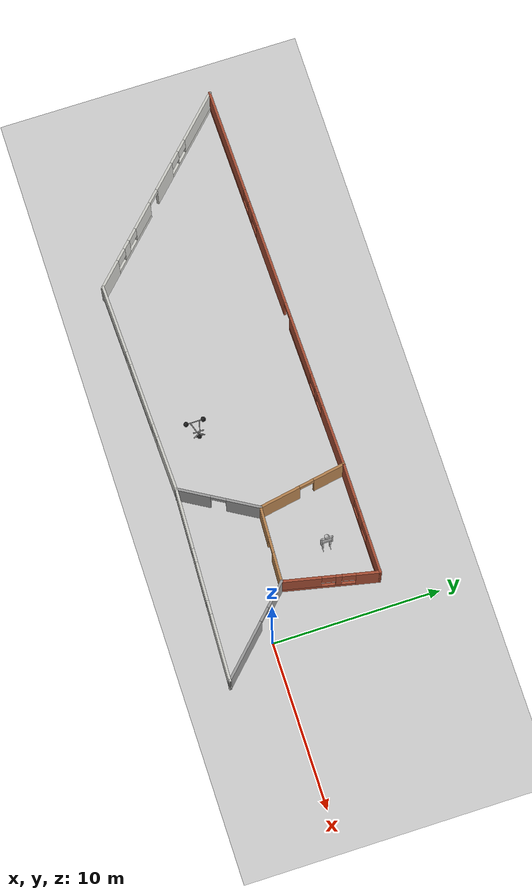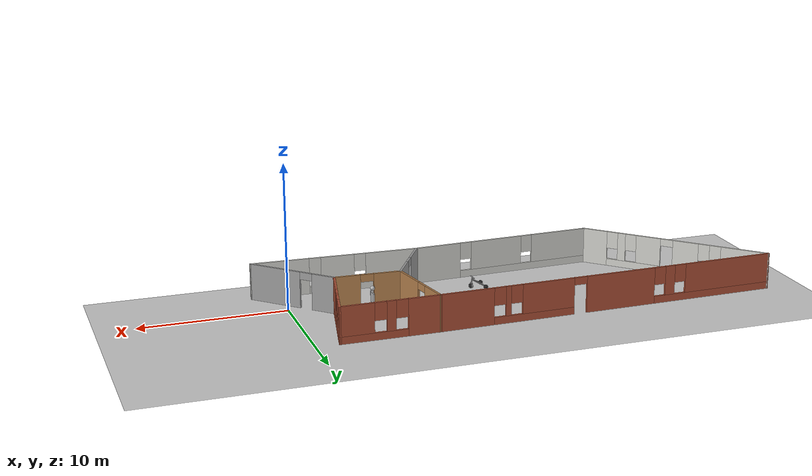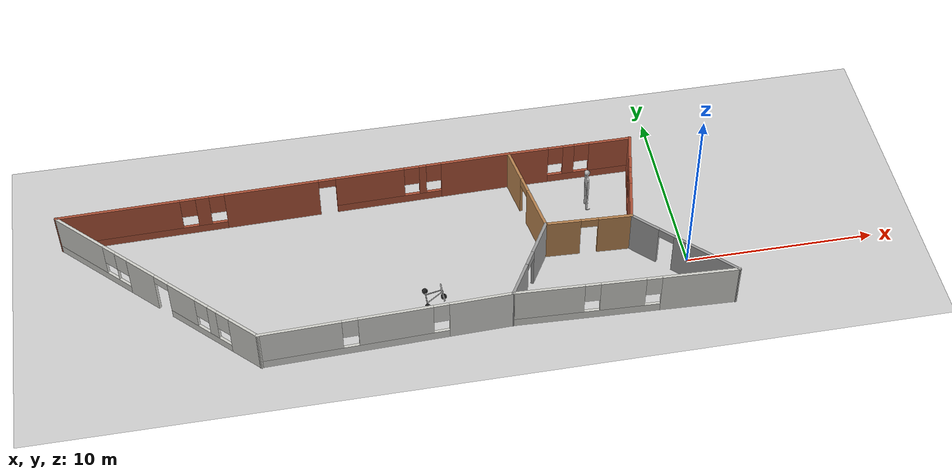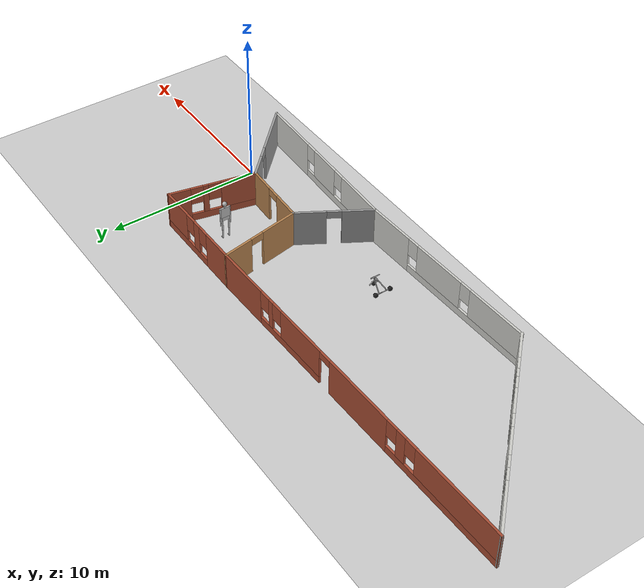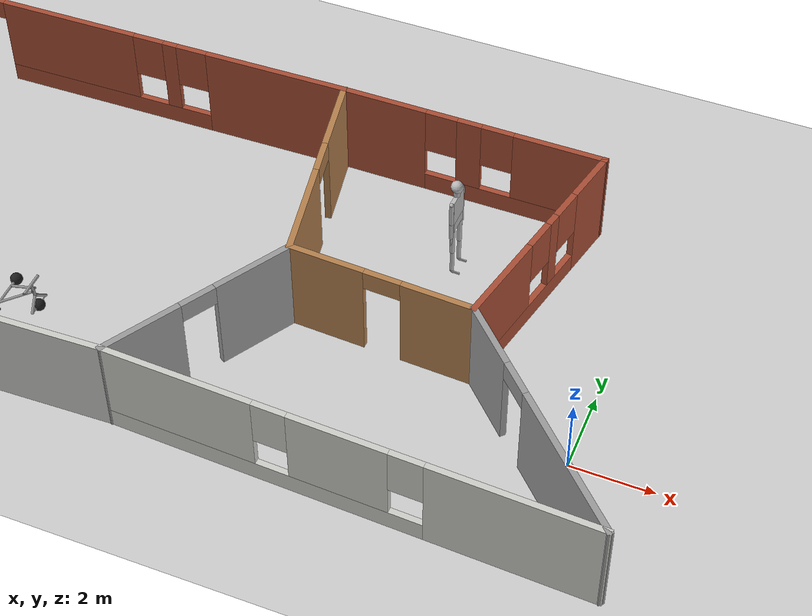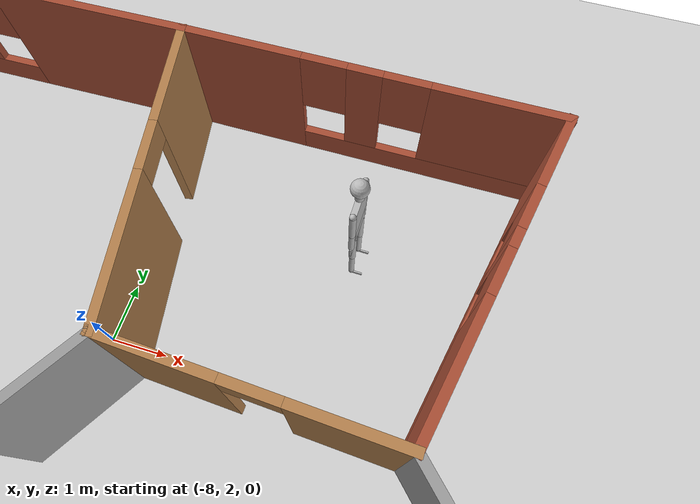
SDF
<sdf version="1.6">
 <world name="default">
  <light name="sun" type="directional">
   <pose>0 0 10 0 -0 0</pose>
   <diffuse>0.8 0.8 0.8 1</diffuse>
   <specular>0.2 0.2 0.2 1</specular>
   <attenuation>
    <range>1000</range>
    <constant>0.9</constant>
    <linear>0.01</linear>
    <quadratic>0.001</quadratic>
   </attenuation>
   <direction>-0.5 0.1 -0.9</direction>
  </light>
  <model name="ground_plane">
   <static>1</static>
   <link name="link">
    <collision name="collision">
     <geometry><plane><normal>0 0 1</normal><size>100 100</size></plane></geometry>
     <surface>
      <contact><collide_bitmask>65535</collide_bitmask></contact>
      <friction><ode><mu>100</mu><mu2>50</mu2></ode></friction>
     </surface>
    </collision>
    <visual name="visual">
     <cast_shadows>0</cast_shadows>
     <geometry><plane><normal>0 0 1</normal><size>100 100</size></plane></geometry>
     <material>
      <script><uri>file://media/materials/scripts/gazebo.material</uri><name>Gazebo/Grey</name></script>
     </material>
    </visual>
   </link>
  </model>
  <gravity>0 0 -9.8</gravity>
  <magnetic_field>6e-06 2.3e-05 -4.2e-05</magnetic_field>
  <atmosphere type="adiabatic"/>
  <physics name="default_physics" default="0" type="ode">
   <max_step_size>0.001</max_step_size>
   <real_time_factor>1</real_time_factor>
   <real_time_update_rate>1000</real_time_update_rate>
  </physics>
  <scene><ambient>0.4 0.4 0.4 1</ambient><background>0.7 0.7 0.7 1</background><shadows>1</shadows></scene>
  <spherical_coordinates>
   <surface_model>EARTH_WGS84</surface_model>
   <latitude_deg>0</latitude_deg>
   <longitude_deg>0</longitude_deg>
   <elevation>0</elevation>
   <heading_deg>0</heading_deg>
  </spherical_coordinates>
  <model name="world2.world">
   <pose>-15.0932 1.90724 0 0 -0 0</pose>
   <link name="Wall_12">
    <pose>-4.95249 4.76552 0 0 0 -3.12282</pose>
    <visual name="Wall_12_Visual_0">
     <pose>-10.0777 0 1.25 0 -0 0</pose>
     <geometry><box><size>3.72695 0.15 2.5</size></box></geometry>
     <material>
      <script><uri>file://media/materials/scripts/gazebo.material</uri><name>Gazebo/Bricks</name></script>
      <ambient>1 1 1 1</ambient>
     </material>
     <meta><layer>0</layer></meta>
    </visual>
    <collision name="Wall_12_Collision_0">
     <geometry><box><size>3.72695 0.15 2.5</size></box></geometry>
     <pose>-10.0777 0 1.25 0 -0 0</pose>
    </collision>
    <visual name="Wall_12_Visual_1">
     <pose>0.770194 0 1.25 0 -0 0</pose>
     <geometry><box><size>4.93565 0.15 2.5</size></box></geometry>
     <material>
      <script><uri>file://media/materials/scripts/gazebo.material</uri><name>Gazebo/Bricks</name></script>
      <ambient>1 1 1 1</ambient>
     </material>
     <meta><layer>0</layer></meta>
    </visual>
    <collision name="Wall_12_Collision_1">
     <geometry><box><size>4.93565 0.15 2.5</size></box></geometry>
     <pose>0.770194 0 1.25 0 -0 0</pose>
    </collision>
    <visual name="Wall_12_Visual_2">
     <pose>-5.40592 0 0.25 0 -0 0</pose>
     <geometry><box><size>5.61658 0.15 0.5</size></box></geometry>
     <material>
      <script><uri>file://media/materials/scripts/gazebo.material</uri><name>Gazebo/Bricks</name></script>
      <ambient>1 1 1 1</ambient>
     </material>
     <meta><layer>0</layer></meta>
    </visual>
    <collision name="Wall_12_Collision_2">
     <geometry><box><size>5.61658 0.15 0.5</size></box></geometry>
     <pose>-5.40592 0 0.25 0 -0 0</pose>
    </collision>
    <visual name="Wall_12_Visual_3">
     <pose>7.58959 0 0.25 0 -0 0</pose>
     <geometry><box><size>8.70314 0.15 0.5</size></box></geometry>
     <material>
      <script><uri>file://media/materials/scripts/gazebo.material</uri><name>Gazebo/Bricks</name></script>
      <ambient>1 1 1 1</ambient>
     </material>
     <meta><layer>0</layer></meta>
    </visual>
    <collision name="Wall_12_Collision_3">
     <geometry><box><size>8.70314 0.15 0.5</size></box></geometry>
     <pose>7.58959 0 0.25 0 -0 0</pose>
    </collision>
    <visual name="Wall_12_Visual_4">
     <pose>-7.22695 0 1.5 0 -0 0</pose>
     <geometry><box><size>0.374523 0.15 2</size></box></geometry>
     <material>
      <script><uri>file://media/materials/scripts/gazebo.material</uri><name>Gazebo/Bricks</name></script>
      <ambient>1 1 1 1</ambient>
     </material>
     <meta><layer>0</layer></meta>
    </visual>
    <collision name="Wall_12_Collision_4">
     <geometry><box><size>0.374523 0.15 2</size></box></geometry>
     <pose>-7.22695 0 1.5 0 -0 0</pose>
    </collision>
    <visual name="Wall_12_Visual_5">
     <pose>-4.41866 0 1.5 0 -0 0</pose>
     <geometry><box><size>3.64206 0.15 2</size></box></geometry>
     <material>
      <script><uri>file://media/materials/scripts/gazebo.material</uri><name>Gazebo/Bricks</name></script>
      <ambient>1 1 1 1</ambient>
     </material>
     <meta><layer>0</layer></meta>
    </visual>
    <collision name="Wall_12_Collision_5">
     <geometry><box><size>3.64206 0.15 2</size></box></geometry>
     <pose>-4.41866 0 1.5 0 -0 0</pose>
    </collision>
    <visual name="Wall_12_Visual_6">
     <pose>-4.41866 0 1.5 0 -0 0</pose>
     <geometry><box><size>3.64206 0.15 2</size></box></geometry>
     <material>
      <script><uri>file://media/materials/scripts/gazebo.material</uri><name>Gazebo/Bricks</name></script>
      <ambient>1 1 1 1</ambient>
     </material>
     <meta><layer>0</layer></meta>
    </visual>
    <collision name="Wall_12_Collision_6">
     <geometry><box><size>3.64206 0.15 2</size></box></geometry>
     <pose>-4.41866 0 1.5 0 -0 0</pose>
    </collision>
    <visual name="Wall_12_Visual_7">
     <pose>4.38859 0 1.5 0 -0 0</pose>
     <geometry><box><size>0.70115 0.15 2</size></box></geometry>
     <material>
      <script><uri>file://media/materials/scripts/gazebo.material</uri><name>Gazebo/Bricks</name></script>
      <ambient>1 1 1 1</ambient>
     </material>
     <meta><layer>0</layer></meta>
    </visual>
    <collision name="Wall_12_Collision_7">
     <geometry><box><size>0.70115 0.15 2</size></box></geometry>
     <pose>4.38859 0 1.5 0 -0 0</pose>
    </collision>
    <visual name="Wall_12_Visual_8">
     <pose>8.74016 0 1.5 0 -0 0</pose>
     <geometry><box><size>6.40199 0.15 2</size></box></geometry>
     <material>
      <script><uri>file://media/materials/scripts/gazebo.material</uri><name>Gazebo/Bricks</name></script>
      <ambient>1 1 1 1</ambient>
     </material>
     <meta><layer>0</layer></meta>
    </visual>
    <collision name="Wall_12_Collision_8">
     <geometry><box><size>6.40199 0.15 2</size></box></geometry>
     <pose>8.74016 0 1.5 0 -0 0</pose>
    </collision>
    <visual name="Wall_12_Visual_9">
     <pose>-7.81421 0 1.9 0 -0 0</pose>
     <geometry><box><size>0.8 0.15 1.2</size></box></geometry>
     <material>
      <script><uri>file://media/materials/scripts/gazebo.material</uri><name>Gazebo/Bricks</name></script>
      <ambient>1 1 1 1</ambient>
     </material>
     <meta><layer>0</layer></meta>
    </visual>
    <collision name="Wall_12_Collision_9">
     <geometry><box><size>0.8 0.15 1.2</size></box></geometry>
     <pose>-7.81421 0 1.9 0 -0 0</pose>
    </collision>
    <visual name="Wall_12_Visual_10">
     <pose>3.63802 0 1.9 0 -0 0</pose>
     <geometry><box><size>0.8 0.15 1.2</size></box></geometry>
     <material>
      <script><uri>file://media/materials/scripts/gazebo.material</uri><name>Gazebo/Bricks</name></script>
      <ambient>1 1 1 1</ambient>
     </material>
     <meta><layer>0</layer></meta>
    </visual>
    <collision name="Wall_12_Collision_10">
     <geometry><box><size>0.8 0.15 1.2</size></box></geometry>
     <pose>3.63802 0 1.9 0 -0 0</pose>
    </collision>
    <visual name="Wall_12_Visual_11">
     <pose>-6.63969 0 1.9 0 -0 0</pose>
     <geometry><box><size>0.8 0.15 1.2</size></box></geometry>
     <material>
      <script><uri>file://media/materials/scripts/gazebo.material</uri><name>Gazebo/Bricks</name></script>
      <ambient>1 1 1 1</ambient>
     </material>
     <meta><layer>0</layer></meta>
    </visual>
    <collision name="Wall_12_Collision_11">
     <geometry><box><size>0.8 0.15 1.2</size></box></geometry>
     <pose>-6.63969 0 1.9 0 -0 0</pose>
    </collision>
    <visual name="Wall_12_Visual_12">
     <pose>5.13917 0 1.9 0 -0 0</pose>
     <geometry><box><size>0.8 0.15 1.2</size></box></geometry>
     <material>
      <script><uri>file://media/materials/scripts/gazebo.material</uri><name>Gazebo/Bricks</name></script>
      <ambient>1 1 1 1</ambient>
     </material>
     <meta><layer>0</layer></meta>
    </visual>
    <collision name="Wall_12_Collision_12">
     <geometry><box><size>0.8 0.15 1.2</size></box></geometry>
     <pose>5.13917 0 1.9 0 -0 0</pose>
    </collision>
    <visual name="Wall_12_Visual_13">
     <pose>-2.14763 0 2.25 0 -0 0</pose>
     <geometry><box><size>0.9 0.15 0.5</size></box></geometry>
     <material>
      <script><uri>file://media/materials/scripts/gazebo.material</uri><name>Gazebo/Bricks</name></script>
      <ambient>1 1 1 1</ambient>
     </material>
     <meta><layer>0</layer></meta>
    </visual>
    <collision name="Wall_12_Collision_13">
     <geometry><box><size>0.9 0.15 0.5</size></box></geometry>
     <pose>-2.14763 0 2.25 0 -0 0</pose>
    </collision>
    <visual name="Wall_12_Visual_14">
     <pose>-2.14763 0 2.25 0 -0 0</pose>
     <geometry><box><size>0.9 0.15 0.5</size></box></geometry>
     <material>
      <script><uri>file://media/materials/scripts/gazebo.material</uri><name>Gazebo/Bricks</name></script>
      <ambient>1 1 1 1</ambient>
     </material>
     <meta><layer>0</layer></meta>
    </visual>
    <collision name="Wall_12_Collision_14">
     <geometry><box><size>0.9 0.15 0.5</size></box></geometry>
     <pose>-2.14763 0 2.25 0 -0 0</pose>
    </collision>
   </link>
   <link name="Wall_14">
    <pose>10.0928 -0.379224 0 0 -0 3.09595</pose>
    <visual name="Wall_14_Visual_0">
     <pose>-1.40364 0 1.25 0 -0 0</pose>
     <geometry><box><size>1.81471 0.15 2.5</size></box></geometry>
     <material>
      <script><uri>file://media/materials/scripts/gazebo.material</uri><name>Gazebo/Wood</name></script>
      <ambient>1 1 1 1</ambient>
     </material>
     <meta><layer>0</layer></meta>
    </visual>
    <collision name="Wall_14_Collision_0">
     <geometry><box><size>1.81471 0.15 2.5</size></box></geometry>
     <pose>-1.40364 0 1.25 0 -0 0</pose>
    </collision>
    <visual name="Wall_14_Visual_1">
     <pose>1.35736 0 1.25 0 -0 0</pose>
     <geometry><box><size>1.90729 0.15 2.5</size></box></geometry>
     <material>
      <script><uri>file://media/materials/scripts/gazebo.material</uri><name>Gazebo/Wood</name></script>
      <ambient>1 1 1 1</ambient>
     </material>
     <meta><layer>0</layer></meta>
    </visual>
    <collision name="Wall_14_Collision_1">
     <geometry><box><size>1.90729 0.15 2.5</size></box></geometry>
     <pose>1.35736 0 1.25 0 -0 0</pose>
    </collision>
    <visual name="Wall_14_Visual_2">
     <pose>-0.046289 0 2.25 0 -0 0</pose>
     <geometry><box><size>0.9 0.15 0.5</size></box></geometry>
     <material>
      <script><uri>file://media/materials/scripts/gazebo.material</uri><name>Gazebo/Wood</name></script>
      <ambient>1 1 1 1</ambient>
     </material>
     <meta><layer>0</layer></meta>
    </visual>
    <collision name="Wall_14_Collision_2">
     <geometry><box><size>0.9 0.15 0.5</size></box></geometry>
     <pose>-0.046289 0 2.25 0 -0 0</pose>
    </collision>
   </link>
   <link name="Wall_15">
    <pose>7.38534 2.35554 0 0 -0 1.74884</pose>
    <visual name="Wall_15_Visual_0">
     <pose>-1.46156 0 1.25 0 -0 0</pose>
     <geometry><box><size>2.57692 0.15 2.5</size></box></geometry>
     <material>
      <script><uri>file://media/materials/scripts/gazebo.material</uri><name>Gazebo/Wood</name></script>
      <ambient>1 1 1 1</ambient>
     </material>
     <meta><layer>0</layer></meta>
    </visual>
    <collision name="Wall_15_Collision_0">
     <geometry><box><size>2.57692 0.15 2.5</size></box></geometry>
     <pose>-1.46156 0 1.25 0 -0 0</pose>
    </collision>
    <visual name="Wall_15_Visual_1">
     <pose>1.73846 0 1.25 0 -0 0</pose>
     <geometry><box><size>2.02311 0.15 2.5</size></box></geometry>
     <material>
      <script><uri>file://media/materials/scripts/gazebo.material</uri><name>Gazebo/Wood</name></script>
      <ambient>1 1 1 1</ambient>
     </material>
     <meta><layer>0</layer></meta>
    </visual>
    <collision name="Wall_15_Collision_1">
     <geometry><box><size>2.02311 0.15 2.5</size></box></geometry>
     <pose>1.73846 0 1.25 0 -0 0</pose>
    </collision>
    <visual name="Wall_15_Visual_2">
     <pose>0.276903 0 2.25 0 -0 0</pose>
     <geometry><box><size>0.9 0.15 0.5</size></box></geometry>
     <material>
      <script><uri>file://media/materials/scripts/gazebo.material</uri><name>Gazebo/Wood</name></script>
      <ambient>1 1 1 1</ambient>
     </material>
     <meta><layer>0</layer></meta>
    </visual>
    <collision name="Wall_15_Collision_2">
     <geometry><box><size>0.9 0.15 0.5</size></box></geometry>
     <pose>0.276903 0 2.25 0 -0 0</pose>
    </collision>
   </link>
   <link name="Wall_16">
    <pose>10.2116 4.98827 0 0 -0 0</pose>
    <visual name="Wall_16_Visual_0">
     <pose>-2.26625 0 1.25 0 -0 0</pose>
     <geometry><box><size>2.21751 0.15 2.5</size></box></geometry>
     <material>
      <script><uri>file://media/materials/scripts/gazebo.material</uri><name>Gazebo/Bricks</name></script>
      <ambient>1 1 1 1</ambient>
     </material>
     <meta><layer>0</layer></meta>
    </visual>
    <collision name="Wall_16_Collision_0">
     <geometry><box><size>2.21751 0.15 2.5</size></box></geometry>
     <pose>-2.26625 0 1.25 0 -0 0</pose>
    </collision>
    <visual name="Wall_16_Visual_1">
     <pose>1.10875 0 0.25 0 -0 0</pose>
     <geometry><box><size>4.53249 0.15 0.5</size></box></geometry>
     <material>
      <script><uri>file://media/materials/scripts/gazebo.material</uri><name>Gazebo/Bricks</name></script>
      <ambient>1 1 1 1</ambient>
     </material>
     <meta><layer>0</layer></meta>
    </visual>
    <collision name="Wall_16_Collision_1">
     <geometry><box><size>4.53249 0.15 0.5</size></box></geometry>
     <pose>1.10875 0 0.25 0 -0 0</pose>
    </collision>
    <visual name="Wall_16_Visual_2">
     <pose>-0.049523 0 1.5 0 -0 0</pose>
     <geometry><box><size>0.615945 0.15 2</size></box></geometry>
     <material>
      <script><uri>file://media/materials/scripts/gazebo.material</uri><name>Gazebo/Bricks</name></script>
      <ambient>1 1 1 1</ambient>
     </material>
     <meta><layer>0</layer></meta>
    </visual>
    <collision name="Wall_16_Collision_2">
     <geometry><box><size>0.615945 0.15 2</size></box></geometry>
     <pose>-0.049523 0 1.5 0 -0 0</pose>
    </collision>
    <visual name="Wall_16_Visual_3">
     <pose>2.21672 0 1.5 0 -0 0</pose>
     <geometry><box><size>2.31655 0.15 2</size></box></geometry>
     <material>
      <script><uri>file://media/materials/scripts/gazebo.material</uri><name>Gazebo/Bricks</name></script>
      <ambient>1 1 1 1</ambient>
     </material>
     <meta><layer>0</layer></meta>
    </visual>
    <collision name="Wall_16_Collision_3">
     <geometry><box><size>2.31655 0.15 2</size></box></geometry>
     <pose>2.21672 0 1.5 0 -0 0</pose>
    </collision>
    <visual name="Wall_16_Visual_4">
     <pose>-0.757495 0 1.9 0 -0 0</pose>
     <geometry><box><size>0.8 0.15 1.2</size></box></geometry>
     <material>
      <script><uri>file://media/materials/scripts/gazebo.material</uri><name>Gazebo/Bricks</name></script>
      <ambient>1 1 1 1</ambient>
     </material>
     <meta><layer>0</layer></meta>
    </visual>
    <collision name="Wall_16_Collision_4">
     <geometry><box><size>0.8 0.15 1.2</size></box></geometry>
     <pose>-0.757495 0 1.9 0 -0 0</pose>
    </collision>
    <visual name="Wall_16_Visual_5">
     <pose>0.65845 0 1.9 0 -0 0</pose>
     <geometry><box><size>0.8 0.15 1.2</size></box></geometry>
     <material>
      <script><uri>file://media/materials/scripts/gazebo.material</uri><name>Gazebo/Bricks</name></script>
      <ambient>1 1 1 1</ambient>
     </material>
     <meta><layer>0</layer></meta>
    </visual>
    <collision name="Wall_16_Collision_5">
     <geometry><box><size>0.8 0.15 1.2</size></box></geometry>
     <pose>0.65845 0 1.9 0 -0 0</pose>
    </collision>
   </link>
   <link name="Wall_17">
    <pose>12.919 2.25351 0 0 0 -1.78418</pose>
    <visual name="Wall_17_Visual_0">
     <pose>-2.14884 0 1.25 0 -0 0</pose>
     <geometry><box><size>1.44877 0.15 2.5</size></box></geometry>
     <material>
      <script><uri>file://media/materials/scripts/gazebo.material</uri><name>Gazebo/Bricks</name></script>
      <ambient>1 1 1 1</ambient>
     </material>
     <meta><layer>0</layer></meta>
    </visual>
    <collision name="Wall_17_Collision_0">
     <geometry><box><size>1.44877 0.15 2.5</size></box></geometry>
     <pose>-2.14884 0 1.25 0 -0 0</pose>
    </collision>
    <visual name="Wall_17_Visual_1">
     <pose>0.724385 0 0.25 0 -0 0</pose>
     <geometry><box><size>4.29768 0.15 0.5</size></box></geometry>
     <material>
      <script><uri>file://media/materials/scripts/gazebo.material</uri><name>Gazebo/Bricks</name></script>
      <ambient>1 1 1 1</ambient>
     </material>
     <meta><layer>0</layer></meta>
    </visual>
    <collision name="Wall_17_Collision_1">
     <geometry><box><size>4.29768 0.15 0.5</size></box></geometry>
     <pose>0.724385 0 0.25 0 -0 0</pose>
    </collision>
    <visual name="Wall_17_Visual_2">
     <pose>-0.451153 0 1.5 0 -0 0</pose>
     <geometry><box><size>0.346603 0.15 2</size></box></geometry>
     <material>
      <script><uri>file://media/materials/scripts/gazebo.material</uri><name>Gazebo/Bricks</name></script>
      <ambient>1 1 1 1</ambient>
     </material>
     <meta><layer>0</layer></meta>
    </visual>
    <collision name="Wall_17_Collision_2">
     <geometry><box><size>0.346603 0.15 2</size></box></geometry>
     <pose>-0.451153 0 1.5 0 -0 0</pose>
    </collision>
    <visual name="Wall_17_Visual_3">
     <pose>1.69769 0 1.5 0 -0 0</pose>
     <geometry><box><size>2.35108 0.15 2</size></box></geometry>
     <material>
      <script><uri>file://media/materials/scripts/gazebo.material</uri><name>Gazebo/Bricks</name></script>
      <ambient>1 1 1 1</ambient>
     </material>
     <meta><layer>0</layer></meta>
    </visual>
    <collision name="Wall_17_Collision_3">
     <geometry><box><size>2.35108 0.15 2</size></box></geometry>
     <pose>1.69769 0 1.5 0 -0 0</pose>
    </collision>
    <visual name="Wall_17_Visual_4">
     <pose>-1.02445 0 1.9 0 -0 0</pose>
     <geometry><box><size>0.8 0.15 1.2</size></box></geometry>
     <material>
      <script><uri>file://media/materials/scripts/gazebo.material</uri><name>Gazebo/Bricks</name></script>
      <ambient>1 1 1 1</ambient>
     </material>
     <meta><layer>0</layer></meta>
    </visual>
    <collision name="Wall_17_Collision_4">
     <geometry><box><size>0.8 0.15 1.2</size></box></geometry>
     <pose>-1.02445 0 1.9 0 -0 0</pose>
    </collision>
    <visual name="Wall_17_Visual_5">
     <pose>0.122148 0 1.9 0 -0 0</pose>
     <geometry><box><size>0.8 0.15 1.2</size></box></geometry>
     <material>
      <script><uri>file://media/materials/scripts/gazebo.material</uri><name>Gazebo/Bricks</name></script>
      <ambient>1 1 1 1</ambient>
     </material>
     <meta><layer>0</layer></meta>
    </visual>
    <collision name="Wall_17_Collision_5">
     <geometry><box><size>0.8 0.15 1.2</size></box></geometry>
     <pose>0.122148 0 1.9 0 -0 0</pose>
    </collision>
   </link>
   <link name="Wall_18">
    <pose>14.5715 -2.72632 0 0 0 -0.785398</pose>
    <visual name="Wall_18_Visual_0">
     <pose>-2.37906 0 1.25 0 -0 0</pose>
     <geometry><box><size>1.74188 0.15 2.5</size></box></geometry>
     <material>
      <script><uri>file://media/materials/scripts/gazebo.material</uri><name>Gazebo/Grey</name></script>
      <ambient>1 1 1 1</ambient>
     </material>
     <meta><layer>0</layer></meta>
    </visual>
    <collision name="Wall_18_Collision_0">
     <geometry><box><size>1.74188 0.15 2.5</size></box></geometry>
     <pose>-2.37906 0 1.25 0 -0 0</pose>
    </collision>
    <visual name="Wall_18_Visual_1">
     <pose>1.32094 0 1.25 0 -0 0</pose>
     <geometry><box><size>3.85812 0.15 2.5</size></box></geometry>
     <material>
      <script><uri>file://media/materials/scripts/gazebo.material</uri><name>Gazebo/Grey</name></script>
      <ambient>1 1 1 1</ambient>
     </material>
     <meta><layer>0</layer></meta>
    </visual>
    <collision name="Wall_18_Collision_1">
     <geometry><box><size>3.85812 0.15 2.5</size></box></geometry>
     <pose>1.32094 0 1.25 0 -0 0</pose>
    </collision>
    <visual name="Wall_18_Visual_2">
     <pose>-1.05812 0 2.25 0 -0 0</pose>
     <geometry><box><size>0.9 0.15 0.5</size></box></geometry>
     <material>
      <script><uri>file://media/materials/scripts/gazebo.material</uri><name>Gazebo/Grey</name></script>
      <ambient>1 1 1 1</ambient>
     </material>
     <meta><layer>0</layer></meta>
    </visual>
    <collision name="Wall_18_Collision_2">
     <geometry><box><size>0.9 0.15 0.5</size></box></geometry>
     <pose>-1.05812 0 2.25 0 -0 0</pose>
    </collision>
   </link>
   <link name="Wall_19">
    <pose>11.0947 -4.7397 0 0 -0 3.10112</pose>
    <visual name="Wall_19_Visual_0">
     <pose>-3.79919 0 1.25 0 -0 0</pose>
     <geometry><box><size>4.00465 0.15 2.5</size></box></geometry>
     <material>
      <script><uri>file://media/materials/scripts/gazebo.material</uri><name>Gazebo/CeilingTiled</name></script>
      <ambient>1 1 1 1</ambient>
     </material>
     <meta><layer>0</layer></meta>
    </visual>
    <collision name="Wall_19_Collision_0">
     <geometry><box><size>4.00465 0.15 2.5</size></box></geometry>
     <pose>-3.79919 0 1.25 0 -0 0</pose>
    </collision>
    <visual name="Wall_19_Visual_1">
     <pose>2.00233 0 0.25 0 -0 0</pose>
     <geometry><box><size>7.59837 0.15 0.5</size></box></geometry>
     <material>
      <script><uri>file://media/materials/scripts/gazebo.material</uri><name>Gazebo/CeilingTiled</name></script>
      <ambient>1 1 1 1</ambient>
     </material>
     <meta><layer>0</layer></meta>
    </visual>
    <collision name="Wall_19_Collision_1">
     <geometry><box><size>7.59837 0.15 0.5</size></box></geometry>
     <pose>2.00233 0 0.25 0 -0 0</pose>
    </collision>
    <visual name="Wall_19_Visual_2">
     <pose>0.162679 0 1.5 0 -0 0</pose>
     <geometry><box><size>2.31908 0.15 2</size></box></geometry>
     <material>
      <script><uri>file://media/materials/scripts/gazebo.material</uri><name>Gazebo/CeilingTiled</name></script>
      <ambient>1 1 1 1</ambient>
     </material>
     <meta><layer>0</layer></meta>
    </visual>
    <collision name="Wall_19_Collision_2">
     <geometry><box><size>2.31908 0.15 2</size></box></geometry>
     <pose>0.162679 0 1.5 0 -0 0</pose>
    </collision>
    <visual name="Wall_19_Visual_3">
     <pose>3.96186 0 1.5 0 -0 0</pose>
     <geometry><box><size>3.6793 0.15 2</size></box></geometry>
     <material>
      <script><uri>file://media/materials/scripts/gazebo.material</uri><name>Gazebo/CeilingTiled</name></script>
      <ambient>1 1 1 1</ambient>
     </material>
     <meta><layer>0</layer></meta>
    </visual>
    <collision name="Wall_19_Collision_3">
     <geometry><box><size>3.6793 0.15 2</size></box></geometry>
     <pose>3.96186 0 1.5 0 -0 0</pose>
    </collision>
    <visual name="Wall_19_Visual_4">
     <pose>-1.39686 0 1.9 0 -0 0</pose>
     <geometry><box><size>0.8 0.15 1.2</size></box></geometry>
     <material>
      <script><uri>file://media/materials/scripts/gazebo.material</uri><name>Gazebo/CeilingTiled</name></script>
      <ambient>1 1 1 1</ambient>
     </material>
     <meta><layer>0</layer></meta>
    </visual>
    <collision name="Wall_19_Collision_4">
     <geometry><box><size>0.8 0.15 1.2</size></box></geometry>
     <pose>-1.39686 0 1.9 0 -0 0</pose>
    </collision>
    <visual name="Wall_19_Visual_5">
     <pose>1.72222 0 1.9 0 -0 0</pose>
     <geometry><box><size>0.8 0.15 1.2</size></box></geometry>
     <material>
      <script><uri>file://media/materials/scripts/gazebo.material</uri><name>Gazebo/CeilingTiled</name></script>
      <ambient>1 1 1 1</ambient>
     </material>
     <meta><layer>0</layer></meta>
    </visual>
    <collision name="Wall_19_Collision_5">
     <geometry><box><size>0.8 0.15 1.2</size></box></geometry>
     <pose>1.72222 0 1.9 0 -0 0</pose>
    </collision>
   </link>
   <link name="Wall_3">
    <pose>-12.0834 -0.199836 0 0 -0 2.35519</pose>
    <visual name="Wall_3_Visual_0">
     <pose>-5.82367 0 1.25 0 -0 0</pose>
     <geometry><box><size>1.90335 0.15 2.5</size></box></geometry>
     <material>
      <script><uri>file://media/materials/scripts/gazebo.material</uri><name>Gazebo/CeilingTiled</name></script>
      <ambient>1 1 1 1</ambient>
     </material>
     <meta><layer>0</layer></meta>
    </visual>
    <collision name="Wall_3_Collision_0">
     <geometry><box><size>1.90335 0.15 2.5</size></box></geometry>
     <pose>-5.82367 0 1.25 0 -0 0</pose>
    </collision>
    <visual name="Wall_3_Visual_1">
     <pose>0.902226 0 1.25 0 -0 0</pose>
     <geometry><box><size>1.83923 0.15 2.5</size></box></geometry>
     <material>
      <script><uri>file://media/materials/scripts/gazebo.material</uri><name>Gazebo/CeilingTiled</name></script>
      <ambient>1 1 1 1</ambient>
     </material>
     <meta><layer>0</layer></meta>
    </visual>
    <collision name="Wall_3_Collision_1">
     <geometry><box><size>1.83923 0.15 2.5</size></box></geometry>
     <pose>0.902226 0 1.25 0 -0 0</pose>
    </collision>
    <visual name="Wall_3_Visual_2">
     <pose>-2.89469 0 0.25 0 -0 0</pose>
     <geometry><box><size>3.95461 0.15 0.5</size></box></geometry>
     <material>
      <script><uri>file://media/materials/scripts/gazebo.material</uri><name>Gazebo/CeilingTiled</name></script>
      <ambient>1 1 1 1</ambient>
     </material>
     <meta><layer>0</layer></meta>
    </visual>
    <collision name="Wall_3_Collision_2">
     <geometry><box><size>3.95461 0.15 0.5</size></box></geometry>
     <pose>-2.89469 0 0.25 0 -0 0</pose>
    </collision>
    <visual name="Wall_3_Visual_3">
     <pose>4.29859 0 0.25 0 -0 0</pose>
     <geometry><box><size>4.95351 0.15 0.5</size></box></geometry>
     <material>
      <script><uri>file://media/materials/scripts/gazebo.material</uri><name>Gazebo/CeilingTiled</name></script>
      <ambient>1 1 1 1</ambient>
     </material>
     <meta><layer>0</layer></meta>
    </visual>
    <collision name="Wall_3_Collision_3">
     <geometry><box><size>4.95351 0.15 0.5</size></box></geometry>
     <pose>4.29859 0 0.25 0 -0 0</pose>
    </collision>
    <visual name="Wall_3_Visual_4">
     <pose>-3.78562 0 1.5 0 -0 0</pose>
     <geometry><box><size>0.572763 0.15 2</size></box></geometry>
     <material>
      <script><uri>file://media/materials/scripts/gazebo.material</uri><name>Gazebo/CeilingTiled</name></script>
      <ambient>1 1 1 1</ambient>
     </material>
     <meta><layer>0</layer></meta>
    </visual>
    <collision name="Wall_3_Collision_4">
     <geometry><box><size>0.572763 0.15 2</size></box></geometry>
     <pose>-3.78562 0 1.5 0 -0 0</pose>
    </collision>
    <visual name="Wall_3_Visual_5">
     <pose>-1.80831 0 1.5 0 -0 0</pose>
     <geometry><box><size>1.78185 0.15 2</size></box></geometry>
     <material>
      <script><uri>file://media/materials/scripts/gazebo.material</uri><name>Gazebo/CeilingTiled</name></script>
      <ambient>1 1 1 1</ambient>
     </material>
     <meta><layer>0</layer></meta>
    </visual>
    <collision name="Wall_3_Collision_5">
     <geometry><box><size>1.78185 0.15 2</size></box></geometry>
     <pose>-1.80831 0 1.5 0 -0 0</pose>
    </collision>
    <visual name="Wall_3_Visual_6">
     <pose>-1.80831 0 1.5 0 -0 0</pose>
     <geometry><box><size>1.78185 0.15 2</size></box></geometry>
     <material>
      <script><uri>file://media/materials/scripts/gazebo.material</uri><name>Gazebo/CeilingTiled</name></script>
      <ambient>1 1 1 1</ambient>
     </material>
     <meta><layer>0</layer></meta>
    </visual>
    <collision name="Wall_3_Collision_6">
     <geometry><box><size>1.78185 0.15 2</size></box></geometry>
     <pose>-1.80831 0 1.5 0 -0 0</pose>
    </collision>
    <visual name="Wall_3_Visual_7">
     <pose>2.62227 0 1.5 0 -0 0</pose>
     <geometry><box><size>0.000865 0.15 2</size></box></geometry>
     <material>
      <script><uri>file://media/materials/scripts/gazebo.material</uri><name>Gazebo/CeilingTiled</name></script>
      <ambient>1 1 1 1</ambient>
     </material>
     <meta><layer>0</layer></meta>
    </visual>
    <collision name="Wall_3_Collision_7">
     <geometry><box><size>0.000865 0.15 2</size></box></geometry>
     <pose>2.62227 0 1.5 0 -0 0</pose>
    </collision>
    <visual name="Wall_3_Visual_8">
     <pose>5.09903 0 1.5 0 -0 0</pose>
     <geometry><box><size>3.35264 0.15 2</size></box></geometry>
     <material>
      <script><uri>file://media/materials/scripts/gazebo.material</uri><name>Gazebo/CeilingTiled</name></script>
      <ambient>1 1 1 1</ambient>
     </material>
     <meta><layer>0</layer></meta>
    </visual>
    <collision name="Wall_3_Collision_8">
     <geometry><box><size>3.35264 0.15 2</size></box></geometry>
     <pose>5.09903 0 1.5 0 -0 0</pose>
    </collision>
    <visual name="Wall_3_Visual_9">
     <pose>-4.472 0 1.9 0 -0 0</pose>
     <geometry><box><size>0.8 0.15 1.2</size></box></geometry>
     <material>
      <script><uri>file://media/materials/scripts/gazebo.material</uri><name>Gazebo/CeilingTiled</name></script>
      <ambient>1 1 1 1</ambient>
     </material>
     <meta><layer>0</layer></meta>
    </visual>
    <collision name="Wall_3_Collision_9">
     <geometry><box><size>0.8 0.15 1.2</size></box></geometry>
     <pose>-4.472 0 1.9 0 -0 0</pose>
    </collision>
    <visual name="Wall_3_Visual_10">
     <pose>2.22184 0 1.9 0 -0 0</pose>
     <geometry><box><size>0.8 0.15 1.2</size></box></geometry>
     <material>
      <script><uri>file://media/materials/scripts/gazebo.material</uri><name>Gazebo/CeilingTiled</name></script>
      <ambient>1 1 1 1</ambient>
     </material>
     <meta><layer>0</layer></meta>
    </visual>
    <collision name="Wall_3_Collision_10">
     <geometry><box><size>0.8 0.15 1.2</size></box></geometry>
     <pose>2.22184 0 1.9 0 -0 0</pose>
    </collision>
    <visual name="Wall_3_Visual_11">
     <pose>-3.09924 0 1.9 0 -0 0</pose>
     <geometry><box><size>0.8 0.15 1.2</size></box></geometry>
     <material>
      <script><uri>file://media/materials/scripts/gazebo.material</uri><name>Gazebo/CeilingTiled</name></script>
      <ambient>1 1 1 1</ambient>
     </material>
     <meta><layer>0</layer></meta>
    </visual>
    <collision name="Wall_3_Collision_11">
     <geometry><box><size>0.8 0.15 1.2</size></box></geometry>
     <pose>-3.09924 0 1.9 0 -0 0</pose>
    </collision>
    <visual name="Wall_3_Visual_12">
     <pose>3.02271 0 1.9 0 -0 0</pose>
     <geometry><box><size>0.8 0.15 1.2</size></box></geometry>
     <material>
      <script><uri>file://media/materials/scripts/gazebo.material</uri><name>Gazebo/CeilingTiled</name></script>
      <ambient>1 1 1 1</ambient>
     </material>
     <meta><layer>0</layer></meta>
    </visual>
    <collision name="Wall_3_Collision_12">
     <geometry><box><size>0.8 0.15 1.2</size></box></geometry>
     <pose>3.02271 0 1.9 0 -0 0</pose>
    </collision>
    <visual name="Wall_3_Visual_13">
     <pose>-0.467389 0 2.25 0 -0 0</pose>
     <geometry><box><size>0.9 0.15 0.5</size></box></geometry>
     <material>
      <script><uri>file://media/materials/scripts/gazebo.material</uri><name>Gazebo/CeilingTiled</name></script>
      <ambient>1 1 1 1</ambient>
     </material>
     <meta><layer>0</layer></meta>
    </visual>
    <collision name="Wall_3_Collision_13">
     <geometry><box><size>0.9 0.15 0.5</size></box></geometry>
     <pose>-0.467389 0 2.25 0 -0 0</pose>
    </collision>
    <visual name="Wall_3_Visual_14">
     <pose>-0.467389 0 2.25 0 -0 0</pose>
     <geometry><box><size>0.9 0.15 0.5</size></box></geometry>
     <material>
      <script><uri>file://media/materials/scripts/gazebo.material</uri><name>Gazebo/CeilingTiled</name></script>
      <ambient>1 1 1 1</ambient>
     </material>
     <meta><layer>0</layer></meta>
    </visual>
    <collision name="Wall_3_Collision_14">
     <geometry><box><size>0.9 0.15 0.5</size></box></geometry>
     <pose>-0.467389 0 2.25 0 -0 0</pose>
    </collision>
   </link>
   <link name="Wall_8">
    <pose>6.616 -2.3926 0 0 -0 1.03952</pose>
    <visual name="Wall_8_Visual_0">
     <pose>-1.49065 0 1.25 0 -0 0</pose>
     <geometry><box><size>2.07593 0.15 2.5</size></box></geometry>
     <material>
      <script><uri>file://media/materials/scripts/gazebo.material</uri><name>Gazebo/Grey</name></script>
      <ambient>0 0 0 0</ambient>
     </material>
     <meta><layer>0</layer></meta>
    </visual>
    <collision name="Wall_8_Collision_0">
     <geometry><box><size>2.07593 0.15 2.5</size></box></geometry>
     <pose>-1.49065 0 1.25 0 -0 0</pose>
    </collision>
    <visual name="Wall_8_Visual_1">
     <pose>1.48797 0 1.25 0 -0 0</pose>
     <geometry><box><size>2.0813 0.15 2.5</size></box></geometry>
     <material>
      <script><uri>file://media/materials/scripts/gazebo.material</uri><name>Gazebo/Grey</name></script>
      <ambient>0 0 0 0</ambient>
     </material>
     <meta><layer>0</layer></meta>
    </visual>
    <collision name="Wall_8_Collision_1">
     <geometry><box><size>2.0813 0.15 2.5</size></box></geometry>
     <pose>1.48797 0 1.25 0 -0 0</pose>
    </collision>
    <visual name="Wall_8_Visual_2">
     <pose>-0.002682 0 2.25 0 -0 0</pose>
     <geometry><box><size>0.9 0.15 0.5</size></box></geometry>
     <material>
      <script><uri>file://media/materials/scripts/gazebo.material</uri><name>Gazebo/Grey</name></script>
      <ambient>0 0 0 0</ambient>
     </material>
     <meta><layer>0</layer></meta>
    </visual>
    <collision name="Wall_8_Collision_2">
     <geometry><box><size>0.9 0.15 0.5</size></box></geometry>
     <pose>-0.002682 0 2.25 0 -0 0</pose>
    </collision>
   </link>
   <link name="Wall_9">
    <pose>-1.00401 -4.70993 0 0 0 -3.10994</pose>
    <visual name="Wall_9_Visual_0">
     <pose>-4.79403 0 1.25 0 -0 0</pose>
     <geometry><box><size>3.32217 0.15 2.5</size></box></geometry>
     <material>
      <script><uri>file://media/materials/scripts/gazebo.material</uri><name>Gazebo/CeilingTiled</name></script>
      <ambient>1 1 1 1</ambient>
     </material>
     <meta><layer>0</layer></meta>
    </visual>
    <collision name="Wall_9_Collision_0">
     <geometry><box><size>3.32217 0.15 2.5</size></box></geometry>
     <pose>-4.79403 0 1.25 0 -0 0</pose>
    </collision>
    <visual name="Wall_9_Visual_1">
     <pose>1.66108 0 0.25 0 -0 0</pose>
     <geometry><box><size>9.58806 0.15 0.5</size></box></geometry>
     <material>
      <script><uri>file://media/materials/scripts/gazebo.material</uri><name>Gazebo/CeilingTiled</name></script>
      <ambient>1 1 1 1</ambient>
     </material>
     <meta><layer>0</layer></meta>
    </visual>
    <collision name="Wall_9_Collision_1">
     <geometry><box><size>9.58806 0.15 0.5</size></box></geometry>
     <pose>1.66108 0 0.25 0 -0 0</pose>
    </collision>
    <visual name="Wall_9_Visual_2">
     <pose>-0.447708 0 1.5 0 -0 0</pose>
     <geometry><box><size>3.77047 0.15 2</size></box></geometry>
     <material>
      <script><uri>file://media/materials/scripts/gazebo.material</uri><name>Gazebo/CeilingTiled</name></script>
      <ambient>1 1 1 1</ambient>
     </material>
     <meta><layer>0</layer></meta>
    </visual>
    <collision name="Wall_9_Collision_2">
     <geometry><box><size>3.77047 0.15 2</size></box></geometry>
     <pose>-0.447708 0 1.5 0 -0 0</pose>
    </collision>
    <visual name="Wall_9_Visual_3">
     <pose>4.34632 0 1.5 0 -0 0</pose>
     <geometry><box><size>4.21759 0.15 2</size></box></geometry>
     <material>
      <script><uri>file://media/materials/scripts/gazebo.material</uri><name>Gazebo/CeilingTiled</name></script>
      <ambient>1 1 1 1</ambient>
     </material>
     <meta><layer>0</layer></meta>
    </visual>
    <collision name="Wall_9_Collision_3">
     <geometry><box><size>4.21759 0.15 2</size></box></geometry>
     <pose>4.34632 0 1.5 0 -0 0</pose>
    </collision>
    <visual name="Wall_9_Visual_4">
     <pose>-2.73294 0 1.9 0 -0 0</pose>
     <geometry><box><size>0.8 0.15 1.2</size></box></geometry>
     <material>
      <script><uri>file://media/materials/scripts/gazebo.material</uri><name>Gazebo/CeilingTiled</name></script>
      <ambient>1 1 1 1</ambient>
     </material>
     <meta><layer>0</layer></meta>
    </visual>
    <collision name="Wall_9_Collision_4">
     <geometry><box><size>0.8 0.15 1.2</size></box></geometry>
     <pose>-2.73294 0 1.9 0 -0 0</pose>
    </collision>
    <visual name="Wall_9_Visual_5">
     <pose>1.83753 0 1.9 0 -0 0</pose>
     <geometry><box><size>0.8 0.15 1.2</size></box></geometry>
     <material>
      <script><uri>file://media/materials/scripts/gazebo.material</uri><name>Gazebo/CeilingTiled</name></script>
      <ambient>1 1 1 1</ambient>
     </material>
     <meta><layer>0</layer></meta>
    </visual>
    <collision name="Wall_9_Collision_5">
     <geometry><box><size>0.8 0.15 1.2</size></box></geometry>
     <pose>1.83753 0 1.9 0 -0 0</pose>
    </collision>
   </link>
   <static>1</static>
  </model>
  <model name="ragdoll">
   <pose>-4.39406 4.64494 1.39999 -2e-06 -0.000996 -0.015964</pose>
   <link name="hip">
    <inertial>
     <inertia><ixx>0.1</ixx><ixy>0</ixy><ixz>0</ixz><iyy>0.1</iyy><iyz>0</iyz><izz>0.1</izz></inertia>
     <mass>10</mass>
    </inertial>
    <collision name="hip_geom">
     <pose>0 0 0.125 0 -0 0</pose>
     <geometry><box><size>0.1 0.5 0.25</size></box></geometry>
     <surface>
      <friction><ode><mu>-1</mu><mu2>-1</mu2><fdir1>0 0 0</fdir1><slip1>0</slip1><slip2>0</slip2></ode></friction>
      <bounce><restitution_coefficient>0</restitution_coefficient><threshold>100000</threshold></bounce>
      <contact>
       <ode>
        <soft_cfm>0</soft_cfm>
        <soft_erp>0.2</soft_erp>
        <kp>1e+12</kp>
        <kd>1</kd>
        <max_vel>0</max_vel>
        <min_depth>0.001</min_depth>
       </ode>
      </contact>
     </surface>
    </collision>
    <visual name="hip_geom_visual">
     <pose>0 0 0.125 0 -0 0</pose>
     <geometry><box><size>0.1 0.5 0.25</size></box></geometry>
    </visual>
    <gravity>0</gravity>
   </link>
   <link name="l_thigh_pan">
    <pose>0 0.22 0 0 -0 0</pose>
    <inertial>
     <inertia><ixx>0.01</ixx><ixy>0</ixy><ixz>0</ixz><iyy>0.01</iyy><iyz>0</iyz><izz>0.01</izz></inertia>
     <mass>1</mass>
    </inertial>
    <collision name="l_thigh_pan_geom">
     <pose>0 0 -0.03 0 -0 0</pose>
     <geometry><sphere><radius>0.06</radius></sphere></geometry>
     <surface>
      <friction><ode><mu>-1</mu><mu2>-1</mu2><fdir1>0 0 0</fdir1><slip1>0</slip1><slip2>0</slip2></ode></friction>
      <bounce><restitution_coefficient>0</restitution_coefficient><threshold>100000</threshold></bounce>
      <contact>
       <ode>
        <soft_cfm>0</soft_cfm>
        <soft_erp>0.2</soft_erp>
        <kp>1e+12</kp>
        <kd>1</kd>
        <max_vel>0</max_vel>
        <min_depth>0.001</min_depth>
       </ode>
      </contact>
     </surface>
    </collision>
    <visual name="l_thigh_pan_geom_visual">
     <pose>0 0 -0.03 0 -0 0</pose>
     <geometry><sphere><radius>0.06</radius></sphere></geometry>
    </visual>
    <gravity>0</gravity>
   </link>
   <link name="l_thigh_lift">
    <pose>0 0.22 0 0 -0 0</pose>
    <inertial>
     <inertia><ixx>0.05</ixx><ixy>0</ixy><ixz>0</ixz><iyy>0.05</iyy><iyz>0</iyz><izz>0.05</izz></inertia>
     <mass>5</mass>
    </inertial>
    <collision name="l_thigh_lift_geom">
     <pose>0 0 -0.35 0 -0 0</pose>
     <geometry><cylinder><radius>0.06</radius><length>0.7</length></cylinder></geometry>
     <surface>
      <friction><ode><mu>-1</mu><mu2>-1</mu2><fdir1>0 0 0</fdir1><slip1>0</slip1><slip2>0</slip2></ode></friction>
      <bounce><restitution_coefficient>0</restitution_coefficient><threshold>100000</threshold></bounce>
      <contact>
       <ode>
        <soft_cfm>0</soft_cfm>
        <soft_erp>0.2</soft_erp>
        <kp>1e+12</kp>
        <kd>1</kd>
        <max_vel>0</max_vel>
        <min_depth>0.001</min_depth>
       </ode>
      </contact>
     </surface>
    </collision>
    <visual name="l_thigh_lift_geom_visual">
     <pose>0 0 -0.35 0 -0 0</pose>
     <geometry><cylinder><radius>0.06</radius><length>0.7</length></cylinder></geometry>
    </visual>
    <gravity>0</gravity>
   </link>
   <link name="l_calf">
    <pose>0 0.22 -0.7 0 -0 0</pose>
    <inertial>
     <inertia><ixx>0.02</ixx><ixy>0</ixy><ixz>0</ixz><iyy>0.02</iyy><iyz>0</iyz><izz>0.02</izz></inertia>
     <mass>2</mass>
    </inertial>
    <collision name="l_calf_geom">
     <pose>0 0 -0.3 0 -0 0</pose>
     <geometry><cylinder><radius>0.05</radius><length>0.6</length></cylinder></geometry>
     <surface>
      <friction><ode><mu>-1</mu><mu2>-1</mu2><fdir1>0 0 0</fdir1><slip1>0</slip1><slip2>0</slip2></ode></friction>
      <bounce><restitution_coefficient>0</restitution_coefficient><threshold>100000</threshold></bounce>
      <contact>
       <ode>
        <soft_cfm>0</soft_cfm>
        <soft_erp>0.2</soft_erp>
        <kp>1e+12</kp>
        <kd>1</kd>
        <max_vel>0</max_vel>
        <min_depth>0.001</min_depth>
       </ode>
      </contact>
     </surface>
    </collision>
    <visual name="l_calf_geom_visual">
     <pose>0 0 -0.3 0 -0 0</pose>
     <geometry><cylinder><radius>0.05</radius><length>0.6</length></cylinder></geometry>
    </visual>
    <gravity>0</gravity>
   </link>
   <link name="l_ankle">
    <pose>0 0.22 -1.325 0 -0 0</pose>
    <inertial>
     <inertia><ixx>0.01</ixx><ixy>0</ixy><ixz>0</ixz><iyy>0.01</iyy><iyz>0</iyz><izz>0.01</izz></inertia>
     <mass>1</mass>
    </inertial>
    <collision name="l_ankle_geom">
     <geometry><sphere><radius>0.05</radius></sphere></geometry>
     <surface>
      <friction><ode><mu>-1</mu><mu2>-1</mu2><fdir1>0 0 0</fdir1><slip1>0</slip1><slip2>0</slip2></ode></friction>
      <bounce><restitution_coefficient>0</restitution_coefficient><threshold>100000</threshold></bounce>
      <contact>
       <ode>
        <soft_cfm>0</soft_cfm>
        <soft_erp>0.2</soft_erp>
        <kp>1e+12</kp>
        <kd>1</kd>
        <max_vel>0</max_vel>
        <min_depth>0.001</min_depth>
       </ode>
      </contact>
     </surface>
    </collision>
    <visual name="l_ankle_geom_visual"><geometry><sphere><radius>0.05</radius></sphere></geometry></visual>
    <gravity>0</gravity>
   </link>
   <link name="l_foot">
    <pose>0 0.22 -1.35 0 -0 0</pose>
    <inertial>
     <pose>0.1 0 0 0 -0 0</pose>
     <inertia><ixx>0.01</ixx><ixy>0</ixy><ixz>0</ixz><iyy>0.01</iyy><iyz>0</iyz><izz>0.01</izz></inertia>
     <mass>1</mass>
    </inertial>
    <collision name="l_foot_geom">
     <pose>0.1 0 -0.025 0 -0 0</pose>
     <geometry><box><size>0.2 0.03 0.05</size></box></geometry>
     <surface>
      <friction><ode><mu>-1</mu><mu2>-1</mu2><fdir1>0 0 0</fdir1><slip1>0</slip1><slip2>0</slip2></ode></friction>
      <bounce><restitution_coefficient>0</restitution_coefficient><threshold>100000</threshold></bounce>
      <contact>
       <ode>
        <soft_cfm>0</soft_cfm>
        <soft_erp>0.2</soft_erp>
        <kp>1e+12</kp>
        <kd>1</kd>
        <max_vel>0</max_vel>
        <min_depth>0.001</min_depth>
       </ode>
      </contact>
     </surface>
    </collision>
    <visual name="l_foot_geom_visual">
     <pose>0.1 0 -0.025 0 -0 0</pose>
     <geometry><box><size>0.2 0.03 0.05</size></box></geometry>
    </visual>
   </link>
   <link name="r_thigh_pan">
    <pose>0 -0.22 0 0 -0 0</pose>
    <inertial>
     <inertia><ixx>0.01</ixx><ixy>0</ixy><ixz>0</ixz><iyy>0.01</iyy><iyz>0</iyz><izz>0.01</izz></inertia>
     <mass>1</mass>
    </inertial>
    <collision name="r_thigh_pan_geom">
     <pose>0 0 -0.03 0 -0 0</pose>
     <geometry><sphere><radius>0.06</radius></sphere></geometry>
     <surface>
      <friction><ode><mu>-1</mu><mu2>-1</mu2><fdir1>0 0 0</fdir1><slip1>0</slip1><slip2>0</slip2></ode></friction>
      <bounce><restitution_coefficient>0</restitution_coefficient><threshold>100000</threshold></bounce>
      <contact>
       <ode>
        <soft_cfm>0</soft_cfm>
        <soft_erp>0.2</soft_erp>
        <kp>1e+12</kp>
        <kd>1</kd>
        <max_vel>0</max_vel>
        <min_depth>0.001</min_depth>
       </ode>
      </contact>
     </surface>
    </collision>
    <visual name="r_thigh_pan_geom_visual">
     <pose>0 0 -0.03 0 -0 0</pose>
     <geometry><sphere><radius>0.06</radius></sphere></geometry>
    </visual>
    <gravity>0</gravity>
   </link>
   <link name="r_thigh_lift">
    <pose>0 -0.22 0 0 -0 0</pose>
    <inertial>
     <inertia><ixx>0.05</ixx><ixy>0</ixy><ixz>0</ixz><iyy>0.05</iyy><iyz>0</iyz><izz>0.05</izz></inertia>
     <mass>5</mass>
    </inertial>
    <collision name="r_thigh_lift_geom">
     <pose>0 0 -0.35 0 -0 0</pose>
     <geometry><cylinder><radius>0.06</radius><length>0.7</length></cylinder></geometry>
     <surface>
      <friction><ode><mu>-1</mu><mu2>-1</mu2><fdir1>0 0 0</fdir1><slip1>0</slip1><slip2>0</slip2></ode></friction>
      <bounce><restitution_coefficient>0</restitution_coefficient><threshold>100000</threshold></bounce>
      <contact>
       <ode>
        <soft_cfm>0</soft_cfm>
        <soft_erp>0.2</soft_erp>
        <kp>1e+12</kp>
        <kd>1</kd>
        <max_vel>0</max_vel>
        <min_depth>0.001</min_depth>
       </ode>
      </contact>
     </surface>
    </collision>
    <visual name="r_thigh_lift_geom_visual">
     <pose>0 0 -0.35 0 -0 0</pose>
     <geometry><cylinder><radius>0.06</radius><length>0.7</length></cylinder></geometry>
    </visual>
    <gravity>0</gravity>
   </link>
   <link name="r_calf">
    <pose>0 -0.22 -0.7 0 -0 0</pose>
    <inertial>
     <inertia><ixx>0.02</ixx><ixy>0</ixy><ixz>0</ixz><iyy>0.02</iyy><iyz>0</iyz><izz>0.02</izz></inertia>
     <mass>2</mass>
    </inertial>
    <collision name="r_calf_geom">
     <pose>0 0 -0.3 0 -0 0</pose>
     <geometry><cylinder><radius>0.05</radius><length>0.6</length></cylinder></geometry>
     <surface>
      <friction><ode><mu>-1</mu><mu2>-1</mu2><fdir1>0 0 0</fdir1><slip1>0</slip1><slip2>0</slip2></ode></friction>
      <bounce><restitution_coefficient>0</restitution_coefficient><threshold>100000</threshold></bounce>
      <contact>
       <ode>
        <soft_cfm>0</soft_cfm>
        <soft_erp>0.2</soft_erp>
        <kp>1e+12</kp>
        <kd>1</kd>
        <max_vel>0</max_vel>
        <min_depth>0.001</min_depth>
       </ode>
      </contact>
     </surface>
    </collision>
    <visual name="r_calf_geom_visual">
     <pose>0 0 -0.3 0 -0 0</pose>
     <geometry><cylinder><radius>0.05</radius><length>0.6</length></cylinder></geometry>
    </visual>
    <gravity>0</gravity>
   </link>
   <link name="r_ankle">
    <pose>0 -0.22 -1.325 0 -0 0</pose>
    <inertial>
     <inertia><ixx>0.01</ixx><ixy>0</ixy><ixz>0</ixz><iyy>0.01</iyy><iyz>0</iyz><izz>0.01</izz></inertia>
     <mass>1</mass>
    </inertial>
    <collision name="r_ankle_geom">
     <geometry><sphere><radius>0.05</radius></sphere></geometry>
     <surface>
      <friction><ode><mu>-1</mu><mu2>-1</mu2><fdir1>0 0 0</fdir1><slip1>0</slip1><slip2>0</slip2></ode></friction>
      <bounce><restitution_coefficient>0</restitution_coefficient><threshold>100000</threshold></bounce>
      <contact>
       <ode>
        <soft_cfm>0</soft_cfm>
        <soft_erp>0.2</soft_erp>
        <kp>1e+12</kp>
        <kd>1</kd>
        <max_vel>0</max_vel>
        <min_depth>0.001</min_depth>
       </ode>
      </contact>
     </surface>
    </collision>
    <visual name="r_ankle_geom_visual"><geometry><sphere><radius>0.05</radius></sphere></geometry></visual>
    <gravity>0</gravity>
   </link>
   <link name="r_foot">
    <pose>0 -0.22 -1.35 0 -0 0</pose>
    <inertial>
     <pose>0.1 0 0 0 -0 0</pose>
     <inertia><ixx>0.01</ixx><ixy>0</ixy><ixz>0</ixz><iyy>0.01</iyy><iyz>0</iyz><izz>0.01</izz></inertia>
     <mass>1</mass>
    </inertial>
    <collision name="r_foot_geom">
     <pose>0.1 0 -0.025 0 -0 0</pose>
     <geometry><box><size>0.2 0.03 0.05</size></box></geometry>
     <surface>
      <friction><ode><mu>-1</mu><mu2>-1</mu2><fdir1>0 0 0</fdir1><slip1>0</slip1><slip2>0</slip2></ode></friction>
      <bounce><restitution_coefficient>0</restitution_coefficient><threshold>100000</threshold></bounce>
      <contact>
       <ode>
        <soft_cfm>0</soft_cfm>
        <soft_erp>0.2</soft_erp>
        <kp>1e+12</kp>
        <kd>1</kd>
        <max_vel>0</max_vel>
        <min_depth>0.001</min_depth>
       </ode>
      </contact>
     </surface>
    </collision>
    <visual name="r_foot_geom_visual">
     <pose>0.1 0 -0.025 0 -0 0</pose>
     <geometry><box><size>0.2 0.03 0.05</size></box></geometry>
    </visual>
   </link>
   <link name="torso">
    <pose>0 0 0.25 0 -0 0</pose>
    <inertial>
     <inertia><ixx>0.3</ixx><ixy>0</ixy><ixz>0</ixz><iyy>0.3</iyy><iyz>0</iyz><izz>0.3</izz></inertia>
     <mass>30</mass>
    </inertial>
    <collision name="torso_geom">
     <pose>0 0 0.35 0 -0 0</pose>
     <geometry><box><size>0.1 0.6 0.7</size></box></geometry>
     <surface>
      <friction><ode><mu>-1</mu><mu2>-1</mu2><fdir1>0 0 0</fdir1><slip1>0</slip1><slip2>0</slip2></ode></friction>
      <bounce><restitution_coefficient>0</restitution_coefficient><threshold>100000</threshold></bounce>
      <contact>
       <ode>
        <soft_cfm>0</soft_cfm>
        <soft_erp>0.2</soft_erp>
        <kp>1e+12</kp>
        <kd>1</kd>
        <max_vel>0</max_vel>
        <min_depth>0.001</min_depth>
       </ode>
      </contact>
     </surface>
    </collision>
    <visual name="torso_geom_visual">
     <pose>0 0 0.35 0 -0 0</pose>
     <geometry><box><size>0.1 0.6 0.7</size></box></geometry>
    </visual>
    <gravity>0</gravity>
   </link>
   <link name="l_shoulder">
    <pose>0 0.3275 0.9225 0 -0 0</pose>
    <inertial>
     <inertia><ixx>0.01</ixx><ixy>0</ixy><ixz>0</ixz><iyy>0.01</iyy><iyz>0</iyz><izz>0.01</izz></inertia>
     <mass>1</mass>
    </inertial>
    <collision name="l_shoulder_geom">
     <geometry><sphere><radius>0.055</radius></sphere></geometry>
     <surface>
      <friction><ode><mu>-1</mu><mu2>-1</mu2><fdir1>0 0 0</fdir1><slip1>0</slip1><slip2>0</slip2></ode></friction>
      <bounce><restitution_coefficient>0</restitution_coefficient><threshold>100000</threshold></bounce>
      <contact>
       <ode>
        <soft_cfm>0</soft_cfm>
        <soft_erp>0.2</soft_erp>
        <kp>1e+12</kp>
        <kd>1</kd>
        <max_vel>0</max_vel>
        <min_depth>0.001</min_depth>
       </ode>
      </contact>
     </surface>
    </collision>
    <visual name="l_shoulder_geom_visual"><geometry><sphere><radius>0.055</radius></sphere></geometry></visual>
    <gravity>0</gravity>
   </link>
   <link name="l_upper_arm">
    <pose>0 0.3275 0.9225 0 -0 0</pose>
    <inertial>
     <inertia><ixx>0.02</ixx><ixy>0</ixy><ixz>0</ixz><iyy>0.02</iyy><iyz>0</iyz><izz>0.02</izz></inertia>
     <mass>2</mass>
    </inertial>
    <collision name="l_upper_arm_geom">
     <pose>0 0 -0.3 0 -0 0</pose>
     <geometry><cylinder><radius>0.055</radius><length>0.6</length></cylinder></geometry>
     <surface>
      <friction><ode><mu>-1</mu><mu2>-1</mu2><fdir1>0 0 0</fdir1><slip1>0</slip1><slip2>0</slip2></ode></friction>
      <bounce><restitution_coefficient>0</restitution_coefficient><threshold>100000</threshold></bounce>
      <contact>
       <ode>
        <soft_cfm>0</soft_cfm>
        <soft_erp>0.2</soft_erp>
        <kp>1e+12</kp>
        <kd>1</kd>
        <max_vel>0</max_vel>
        <min_depth>0.001</min_depth>
       </ode>
      </contact>
     </surface>
    </collision>
    <visual name="l_upper_arm_geom_visual">
     <pose>0 0 -0.3 0 -0 0</pose>
     <geometry><cylinder><radius>0.055</radius><length>0.6</length></cylinder></geometry>
    </visual>
    <gravity>0</gravity>
   </link>
   <link name="l_forearm">
    <pose>0 0.3275 0.3225 0 -0 0</pose>
    <inertial>
     <inertia><ixx>0.01</ixx><ixy>0</ixy><ixz>0</ixz><iyy>0.01</iyy><iyz>0</iyz><izz>0.01</izz></inertia>
     <mass>1</mass>
    </inertial>
    <collision name="l_forearm_geom">
     <pose>0 0 -0.225 0 -0 0</pose>
     <geometry><cylinder><radius>0.05</radius><length>0.45</length></cylinder></geometry>
     <surface>
      <friction><ode><mu>-1</mu><mu2>-1</mu2><fdir1>0 0 0</fdir1><slip1>0</slip1><slip2>0</slip2></ode></friction>
      <bounce><restitution_coefficient>0</restitution_coefficient><threshold>100000</threshold></bounce>
      <contact>
       <ode>
        <soft_cfm>0</soft_cfm>
        <soft_erp>0.2</soft_erp>
        <kp>1e+12</kp>
        <kd>1</kd>
        <max_vel>0</max_vel>
        <min_depth>0.001</min_depth>
       </ode>
      </contact>
     </surface>
    </collision>
    <visual name="l_forearm_geom_visual">
     <pose>0 0 -0.225 0 -0 0</pose>
     <geometry><cylinder><radius>0.05</radius><length>0.45</length></cylinder></geometry>
    </visual>
    <gravity>0</gravity>
   </link>
   <link name="l_wrist">
    <pose>0 0.3275 -0.1425 0 -0 0</pose>
    <inertial>
     <inertia><ixx>0.01</ixx><ixy>0</ixy><ixz>0</ixz><iyy>0.01</iyy><iyz>0</iyz><izz>0.01</izz></inertia>
     <mass>1</mass>
    </inertial>
    <collision name="l_wrist_geom">
     <geometry><sphere><radius>0.03</radius></sphere></geometry>
     <surface>
      <friction><ode><mu>-1</mu><mu2>-1</mu2><fdir1>0 0 0</fdir1><slip1>0</slip1><slip2>0</slip2></ode></friction>
      <bounce><restitution_coefficient>0</restitution_coefficient><threshold>100000</threshold></bounce>
      <contact>
       <ode>
        <soft_cfm>0</soft_cfm>
        <soft_erp>0.2</soft_erp>
        <kp>1e+12</kp>
        <kd>1</kd>
        <max_vel>0</max_vel>
        <min_depth>0.001</min_depth>
       </ode>
      </contact>
     </surface>
    </collision>
    <visual name="l_wrist_geom_visual"><geometry><sphere><radius>0.03</radius></sphere></geometry></visual>
    <gravity>0</gravity>
   </link>
   <link name="l_hand">
    <pose>0 0.3275 -0.1575 0 -0 0</pose>
    <inertial>
     <inertia><ixx>0.01</ixx><ixy>0</ixy><ixz>0</ixz><iyy>0.01</iyy><iyz>0</iyz><izz>0.01</izz></inertia>
     <mass>1</mass>
    </inertial>
    <collision name="l_hand_geom">
     <pose>0 0 -0.1 0 -0 0</pose>
     <geometry><box><size>0.03 0.1 0.2</size></box></geometry>
     <surface>
      <friction><ode><mu>-1</mu><mu2>-1</mu2><fdir1>0 0 0</fdir1><slip1>0</slip1><slip2>0</slip2></ode></friction>
      <bounce><restitution_coefficient>0</restitution_coefficient><threshold>100000</threshold></bounce>
      <contact>
       <ode>
        <soft_cfm>0</soft_cfm>
        <soft_erp>0.2</soft_erp>
        <kp>1e+12</kp>
        <kd>1</kd>
        <max_vel>0</max_vel>
        <min_depth>0.001</min_depth>
       </ode>
      </contact>
     </surface>
    </collision>
    <visual name="l_hand_geom_visual">
     <pose>0 0 -0.1 0 -0 0</pose>
     <geometry><box><size>0.03 0.1 0.2</size></box></geometry>
    </visual>
    <gravity>0</gravity>
   </link>
   <link name="neck">
    <pose>0 0 0.95 0 -0 0</pose>
    <inertial>
     <inertia><ixx>0.01</ixx><ixy>0</ixy><ixz>0</ixz><iyy>0.01</iyy><iyz>0</iyz><izz>0.01</izz></inertia>
     <mass>1</mass>
    </inertial>
    <collision name="neck_geom">
     <pose>0 0 0.1 0 -0 0</pose>
     <geometry><cylinder><radius>0.075</radius><length>0.2</length></cylinder></geometry>
     <surface>
      <friction><ode><mu>-1</mu><mu2>-1</mu2><fdir1>0 0 0</fdir1><slip1>0</slip1><slip2>0</slip2></ode></friction>
      <bounce><restitution_coefficient>0</restitution_coefficient><threshold>100000</threshold></bounce>
      <contact>
       <ode>
        <soft_cfm>0</soft_cfm>
        <soft_erp>0.2</soft_erp>
        <kp>1e+12</kp>
        <kd>1</kd>
        <max_vel>0</max_vel>
        <min_depth>0.001</min_depth>
       </ode>
      </contact>
     </surface>
    </collision>
    <visual name="neck_geom_visual">
     <pose>0 0 0.1 0 -0 0</pose>
     <geometry><cylinder><radius>0.075</radius><length>0.2</length></cylinder></geometry>
    </visual>
    <gravity>0</gravity>
   </link>
   <link name="head">
    <pose>0 0 1.225 0 -0 0</pose>
    <inertial>
     <inertia><ixx>0.1</ixx><ixy>0</ixy><ixz>0</ixz><iyy>0.1</iyy><iyz>0</iyz><izz>0.1</izz></inertia>
     <mass>10</mass>
    </inertial>
    <collision name="head_geom">
     <geometry><sphere><radius>0.15</radius></sphere></geometry>
     <surface>
      <friction><ode><mu>-1</mu><mu2>-1</mu2><fdir1>0 0 0</fdir1><slip1>0</slip1><slip2>0</slip2></ode></friction>
      <bounce><restitution_coefficient>0</restitution_coefficient><threshold>100000</threshold></bounce>
      <contact>
       <ode>
        <soft_cfm>0</soft_cfm>
        <soft_erp>0.2</soft_erp>
        <kp>1e+12</kp>
        <kd>1</kd>
        <max_vel>0</max_vel>
        <min_depth>0.001</min_depth>
       </ode>
      </contact>
     </surface>
    </collision>
    <visual name="head_geom_visual"><geometry><sphere><radius>0.15</radius></sphere></geometry></visual>
    <gravity>0</gravity>
   </link>
   <link name="r_shoulder">
    <pose>0 -0.3275 0.9225 0 -0 0</pose>
    <inertial>
     <inertia><ixx>0.01</ixx><ixy>0</ixy><ixz>0</ixz><iyy>0.01</iyy><iyz>0</iyz><izz>0.01</izz></inertia>
     <mass>1</mass>
    </inertial>
    <collision name="r_shoulder_geom">
     <geometry><sphere><radius>0.055</radius></sphere></geometry>
     <surface>
      <friction><ode><mu>-1</mu><mu2>-1</mu2><fdir1>0 0 0</fdir1><slip1>0</slip1><slip2>0</slip2></ode></friction>
      <bounce><restitution_coefficient>0</restitution_coefficient><threshold>100000</threshold></bounce>
      <contact>
       <ode>
        <soft_cfm>0</soft_cfm>
        <soft_erp>0.2</soft_erp>
        <kp>1e+12</kp>
        <kd>1</kd>
        <max_vel>0</max_vel>
        <min_depth>0.001</min_depth>
       </ode>
      </contact>
     </surface>
    </collision>
    <visual name="r_shoulder_geom_visual"><geometry><sphere><radius>0.055</radius></sphere></geometry></visual>
    <gravity>0</gravity>
   </link>
   <link name="r_upper_arm">
    <pose>0 -0.3275 0.9225 0 -0 0</pose>
    <inertial>
     <inertia><ixx>0.02</ixx><ixy>0</ixy><ixz>0</ixz><iyy>0.02</iyy><iyz>0</iyz><izz>0.02</izz></inertia>
     <mass>2</mass>
    </inertial>
    <collision name="r_upper_arm_geom">
     <pose>0 0 -0.3 0 -0 0</pose>
     <geometry><cylinder><radius>0.055</radius><length>0.6</length></cylinder></geometry>
     <surface>
      <friction><ode><mu>-1</mu><mu2>-1</mu2><fdir1>0 0 0</fdir1><slip1>0</slip1><slip2>0</slip2></ode></friction>
      <bounce><restitution_coefficient>0</restitution_coefficient><threshold>100000</threshold></bounce>
      <contact>
       <ode>
        <soft_cfm>0</soft_cfm>
        <soft_erp>0.2</soft_erp>
        <kp>1e+12</kp>
        <kd>1</kd>
        <max_vel>0</max_vel>
        <min_depth>0.001</min_depth>
       </ode>
      </contact>
     </surface>
    </collision>
    <visual name="r_upper_arm_geom_visual">
     <pose>0 0 -0.3 0 -0 0</pose>
     <geometry><cylinder><radius>0.055</radius><length>0.6</length></cylinder></geometry>
    </visual>
    <gravity>0</gravity>
   </link>
   <link name="r_forearm">
    <pose>0 -0.3275 0.3225 0 -0 0</pose>
    <inertial>
     <inertia><ixx>0.01</ixx><ixy>0</ixy><ixz>0</ixz><iyy>0.01</iyy><iyz>0</iyz><izz>0.01</izz></inertia>
     <mass>1</mass>
    </inertial>
    <collision name="r_forearm_geom">
     <pose>0 0 -0.225 0 -0 0</pose>
     <geometry><cylinder><radius>0.05</radius><length>0.45</length></cylinder></geometry>
     <surface>
      <friction><ode><mu>-1</mu><mu2>-1</mu2><fdir1>0 0 0</fdir1><slip1>0</slip1><slip2>0</slip2></ode></friction>
      <bounce><restitution_coefficient>0</restitution_coefficient><threshold>100000</threshold></bounce>
      <contact>
       <ode>
        <soft_cfm>0</soft_cfm>
        <soft_erp>0.2</soft_erp>
        <kp>1e+12</kp>
        <kd>1</kd>
        <max_vel>0</max_vel>
        <min_depth>0.001</min_depth>
       </ode>
      </contact>
     </surface>
    </collision>
    <visual name="r_forearm_geom_visual">
     <pose>0 0 -0.225 0 -0 0</pose>
     <geometry><cylinder><radius>0.05</radius><length>0.45</length></cylinder></geometry>
    </visual>
    <gravity>0</gravity>
   </link>
   <link name="r_wrist">
    <pose>0 -0.3275 -0.1425 0 -0 0</pose>
    <inertial>
     <inertia><ixx>0.01</ixx><ixy>0</ixy><ixz>0</ixz><iyy>0.01</iyy><iyz>0</iyz><izz>0.01</izz></inertia>
     <mass>1</mass>
    </inertial>
    <collision name="r_wrist_geom">
     <geometry><sphere><radius>0.03</radius></sphere></geometry>
     <surface>
      <friction><ode><mu>-1</mu><mu2>-1</mu2><fdir1>0 0 0</fdir1><slip1>0</slip1><slip2>0</slip2></ode></friction>
      <bounce><restitution_coefficient>0</restitution_coefficient><threshold>100000</threshold></bounce>
      <contact>
       <ode>
        <soft_cfm>0</soft_cfm>
        <soft_erp>0.2</soft_erp>
        <kp>1e+12</kp>
        <kd>1</kd>
        <max_vel>0</max_vel>
        <min_depth>0.001</min_depth>
       </ode>
      </contact>
     </surface>
    </collision>
    <visual name="r_wrist_geom_visual"><geometry><sphere><radius>0.03</radius></sphere></geometry></visual>
    <gravity>0</gravity>
   </link>
   <link name="r_hand">
    <pose>0 -0.3275 -0.1575 0 -0 0</pose>
    <inertial>
     <inertia><ixx>0.01</ixx><ixy>0</ixy><ixz>0</ixz><iyy>0.01</iyy><iyz>0</iyz><izz>0.01</izz></inertia>
     <mass>1</mass>
    </inertial>
    <collision name="r_hand_geom">
     <pose>0 0 -0.1 0 -0 0</pose>
     <geometry><box><size>0.03 0.1 0.2</size></box></geometry>
     <surface>
      <friction><ode><mu>-1</mu><mu2>-1</mu2><fdir1>0 0 0</fdir1><slip1>0</slip1><slip2>0</slip2></ode></friction>
      <bounce><restitution_coefficient>0</restitution_coefficient><threshold>100000</threshold></bounce>
      <contact>
       <ode>
        <soft_cfm>0</soft_cfm>
        <soft_erp>0.2</soft_erp>
        <kp>1e+12</kp>
        <kd>1</kd>
        <max_vel>0</max_vel>
        <min_depth>0.001</min_depth>
       </ode>
      </contact>
     </surface>
    </collision>
    <visual name="r_hand_geom_visual">
     <pose>0 0 -0.1 0 -0 0</pose>
     <geometry><box><size>0.03 0.1 0.2</size></box></geometry>
    </visual>
    <gravity>0</gravity>
   </link>
   <joint name="l_thigh_pan_joint" type="revolute">
    <parent>hip</parent>
    <child>l_thigh_pan</child>
    <axis>
     <dynamics>
      <damping>0</damping>
      <friction>0</friction>
      <spring_reference>0</spring_reference>
      <spring_stiffness>0</spring_stiffness>
     </dynamics>
     <limit><lower>-1.5708</lower><upper>1.5708</upper><effort>0</effort><velocity>0</velocity></limit>
     <xyz>0 0 1</xyz>
     <use_parent_model_frame>1</use_parent_model_frame>
    </axis>
   </joint>
   <joint name="l_thigh_lift_joint" type="revolute">
    <parent>l_thigh_pan</parent>
    <child>l_thigh_lift</child>
    <axis>
     <dynamics>
      <damping>0</damping>
      <friction>0</friction>
      <spring_reference>0</spring_reference>
      <spring_stiffness>0</spring_stiffness>
     </dynamics>
     <limit><lower>-1.5708</lower><upper>1.5708</upper><effort>0</effort><velocity>0</velocity></limit>
     <xyz>0 1 0</xyz>
     <use_parent_model_frame>1</use_parent_model_frame>
    </axis>
   </joint>
   <joint name="l_calf_joint" type="revolute">
    <parent>l_thigh_lift</parent>
    <child>l_calf</child>
    <axis>
     <dynamics>
      <damping>0</damping>
      <friction>0</friction>
      <spring_reference>0</spring_reference>
      <spring_stiffness>0</spring_stiffness>
     </dynamics>
     <limit><lower>-1.5708</lower><upper>1.5708</upper><effort>0</effort><velocity>0</velocity></limit>
     <xyz>0 1 0</xyz>
     <use_parent_model_frame>1</use_parent_model_frame>
    </axis>
   </joint>
   <joint name="l_ankle_joint" type="revolute">
    <parent>l_calf</parent>
    <child>l_ankle</child>
    <axis>
     <dynamics>
      <damping>0</damping>
      <friction>0</friction>
      <spring_reference>0</spring_reference>
      <spring_stiffness>0</spring_stiffness>
     </dynamics>
     <limit><lower>-1.5708</lower><upper>1.5708</upper><effort>0</effort><velocity>0</velocity></limit>
     <xyz>0 1 0</xyz>
     <use_parent_model_frame>1</use_parent_model_frame>
    </axis>
   </joint>
   <joint name="l_foot_joint" type="revolute">
    <parent>l_ankle</parent>
    <child>l_foot</child>
    <axis>
     <dynamics>
      <damping>0</damping>
      <friction>0</friction>
      <spring_reference>0</spring_reference>
      <spring_stiffness>0</spring_stiffness>
     </dynamics>
     <limit><lower>-1.5708</lower><upper>1.5708</upper><effort>0</effort><velocity>0</velocity></limit>
     <xyz>1 0 0</xyz>
     <use_parent_model_frame>1</use_parent_model_frame>
    </axis>
   </joint>
   <joint name="r_thigh_pan_joint" type="revolute">
    <parent>hip</parent>
    <child>r_thigh_pan</child>
    <axis>
     <dynamics>
      <damping>0</damping>
      <friction>0</friction>
      <spring_reference>0</spring_reference>
      <spring_stiffness>0</spring_stiffness>
     </dynamics>
     <limit><lower>-1.5708</lower><upper>1.5708</upper><effort>0</effort><velocity>0</velocity></limit>
     <xyz>0 0 1</xyz>
     <use_parent_model_frame>1</use_parent_model_frame>
    </axis>
   </joint>
   <joint name="r_thigh_lift_joint" type="revolute">
    <parent>r_thigh_pan</parent>
    <child>r_thigh_lift</child>
    <axis>
     <dynamics>
      <damping>0</damping>
      <friction>0</friction>
      <spring_reference>0</spring_reference>
      <spring_stiffness>0</spring_stiffness>
     </dynamics>
     <limit><lower>-1.5708</lower><upper>1.5708</upper><effort>0</effort><velocity>0</velocity></limit>
     <xyz>0 1 0</xyz>
     <use_parent_model_frame>1</use_parent_model_frame>
    </axis>
   </joint>
   <joint name="r_calf_joint" type="revolute">
    <parent>r_thigh_lift</parent>
    <child>r_calf</child>
    <axis>
     <dynamics>
      <damping>0</damping>
      <friction>0</friction>
      <spring_reference>0</spring_reference>
      <spring_stiffness>0</spring_stiffness>
     </dynamics>
     <limit><lower>-1.5708</lower><upper>1.5708</upper><effort>0</effort><velocity>0</velocity></limit>
     <xyz>0 1 0</xyz>
     <use_parent_model_frame>1</use_parent_model_frame>
    </axis>
   </joint>
   <joint name="r_ankle_joint" type="revolute">
    <parent>r_calf</parent>
    <child>r_ankle</child>
    <axis>
     <dynamics>
      <damping>0</damping>
      <friction>0</friction>
      <spring_reference>0</spring_reference>
      <spring_stiffness>0</spring_stiffness>
     </dynamics>
     <limit><lower>-1.5708</lower><upper>1.5708</upper><effort>0</effort><velocity>0</velocity></limit>
     <xyz>0 1 0</xyz>
     <use_parent_model_frame>1</use_parent_model_frame>
    </axis>
   </joint>
   <joint name="r_foot_joint" type="revolute">
    <parent>r_ankle</parent>
    <child>r_foot</child>
    <axis>
     <dynamics>
      <damping>0</damping>
      <friction>0</friction>
      <spring_reference>0</spring_reference>
      <spring_stiffness>0</spring_stiffness>
     </dynamics>
     <limit><lower>-1.5708</lower><upper>1.5708</upper><effort>0</effort><velocity>0</velocity></limit>
     <xyz>1 0 0</xyz>
     <use_parent_model_frame>1</use_parent_model_frame>
    </axis>
   </joint>
   <joint name="torso_joint" type="revolute">
    <parent>hip</parent>
    <child>torso</child>
    <axis>
     <dynamics>
      <damping>0</damping>
      <friction>0</friction>
      <spring_reference>0</spring_reference>
      <spring_stiffness>0</spring_stiffness>
     </dynamics>
     <limit><lower>-1.5708</lower><upper>1.5708</upper><effort>0</effort><velocity>0</velocity></limit>
     <xyz>0 1 0</xyz>
     <use_parent_model_frame>1</use_parent_model_frame>
    </axis>
   </joint>
   <joint name="l_shoulder_joint" type="revolute">
    <parent>torso</parent>
    <child>l_shoulder</child>
    <axis>
     <dynamics>
      <damping>0</damping>
      <friction>0</friction>
      <spring_reference>0</spring_reference>
      <spring_stiffness>0</spring_stiffness>
     </dynamics>
     <limit><lower>-1.5708</lower><upper>1.5708</upper><effort>0</effort><velocity>0</velocity></limit>
     <xyz>1 0 0</xyz>
     <use_parent_model_frame>1</use_parent_model_frame>
    </axis>
   </joint>
   <joint name="l_upper_arm_joint" type="revolute">
    <parent>l_shoulder</parent>
    <child>l_upper_arm</child>
    <axis>
     <dynamics>
      <damping>0</damping>
      <friction>0</friction>
      <spring_reference>0</spring_reference>
      <spring_stiffness>0</spring_stiffness>
     </dynamics>
     <limit><lower>-1.5708</lower><upper>1.5708</upper><effort>0</effort><velocity>0</velocity></limit>
     <xyz>0 1 0</xyz>
     <use_parent_model_frame>1</use_parent_model_frame>
    </axis>
   </joint>
   <joint name="l_forearm_joint" type="revolute">
    <parent>l_upper_arm</parent>
    <child>l_forearm</child>
    <axis>
     <dynamics>
      <damping>0</damping>
      <friction>0</friction>
      <spring_reference>0</spring_reference>
      <spring_stiffness>0</spring_stiffness>
     </dynamics>
     <limit><lower>-1.5708</lower><upper>1.5708</upper><effort>0</effort><velocity>0</velocity></limit>
     <xyz>0 1 0</xyz>
     <use_parent_model_frame>1</use_parent_model_frame>
    </axis>
   </joint>
   <joint name="l_wrist_joint" type="revolute">
    <parent>l_forearm</parent>
    <child>l_wrist</child>
    <axis>
     <dynamics>
      <damping>0</damping>
      <friction>0</friction>
      <spring_reference>0</spring_reference>
      <spring_stiffness>0</spring_stiffness>
     </dynamics>
     <limit><lower>-1.5708</lower><upper>1.5708</upper><effort>0</effort><velocity>0</velocity></limit>
     <xyz>0 1 0</xyz>
     <use_parent_model_frame>1</use_parent_model_frame>
    </axis>
   </joint>
   <joint name="l_hand_joint" type="revolute">
    <parent>l_wrist</parent>
    <child>l_hand</child>
    <axis>
     <dynamics>
      <damping>0</damping>
      <friction>0</friction>
      <spring_reference>0</spring_reference>
      <spring_stiffness>0</spring_stiffness>
     </dynamics>
     <limit><lower>-1.5708</lower><upper>1.5708</upper><effort>0</effort><velocity>0</velocity></limit>
     <xyz>0 1 0</xyz>
     <use_parent_model_frame>1</use_parent_model_frame>
    </axis>
   </joint>
   <joint name="neck_joint" type="revolute">
    <parent>torso</parent>
    <child>neck</child>
    <axis>
     <dynamics>
      <damping>0</damping>
      <friction>0</friction>
      <spring_reference>0</spring_reference>
      <spring_stiffness>0</spring_stiffness>
     </dynamics>
     <limit><lower>-1.5708</lower><upper>1.5708</upper><effort>0</effort><velocity>0</velocity></limit>
     <xyz>0 0 1</xyz>
     <use_parent_model_frame>1</use_parent_model_frame>
    </axis>
   </joint>
   <joint name="head_joint" type="revolute">
    <parent>neck</parent>
    <child>head</child>
    <axis>
     <dynamics>
      <damping>0</damping>
      <friction>0</friction>
      <spring_reference>0</spring_reference>
      <spring_stiffness>0</spring_stiffness>
     </dynamics>
     <limit><lower>-1.5708</lower><upper>1.5708</upper><effort>0</effort><velocity>0</velocity></limit>
     <xyz>0 1 0</xyz>
     <use_parent_model_frame>1</use_parent_model_frame>
    </axis>
   </joint>
   <joint name="r_shoulder_joint" type="revolute">
    <parent>torso</parent>
    <child>r_shoulder</child>
    <axis>
     <dynamics>
      <damping>0</damping>
      <friction>0</friction>
      <spring_reference>0</spring_reference>
      <spring_stiffness>0</spring_stiffness>
     </dynamics>
     <limit><lower>-1.5708</lower><upper>1.5708</upper><effort>0</effort><velocity>0</velocity></limit>
     <xyz>1 0 0</xyz>
     <use_parent_model_frame>1</use_parent_model_frame>
    </axis>
   </joint>
   <joint name="r_upper_arm_joint" type="revolute">
    <parent>r_shoulder</parent>
    <child>r_upper_arm</child>
    <axis>
     <dynamics>
      <damping>0</damping>
      <friction>0</friction>
      <spring_reference>0</spring_reference>
      <spring_stiffness>0</spring_stiffness>
     </dynamics>
     <limit><lower>-1.5708</lower><upper>1.5708</upper><effort>0</effort><velocity>0</velocity></limit>
     <xyz>0 1 0</xyz>
     <use_parent_model_frame>1</use_parent_model_frame>
    </axis>
   </joint>
   <joint name="r_forearm_joint" type="revolute">
    <parent>r_upper_arm</parent>
    <child>r_forearm</child>
    <axis>
     <dynamics>
      <damping>0</damping>
      <friction>0</friction>
      <spring_reference>0</spring_reference>
      <spring_stiffness>0</spring_stiffness>
     </dynamics>
     <limit><lower>-1.5708</lower><upper>1.5708</upper><effort>0</effort><velocity>0</velocity></limit>
     <xyz>0 1 0</xyz>
     <use_parent_model_frame>1</use_parent_model_frame>
    </axis>
   </joint>
   <joint name="r_wrist_joint" type="revolute">
    <parent>r_forearm</parent>
    <child>r_wrist</child>
    <axis>
     <dynamics>
      <damping>0</damping>
      <friction>0</friction>
      <spring_reference>0</spring_reference>
      <spring_stiffness>0</spring_stiffness>
     </dynamics>
     <limit><lower>-1.5708</lower><upper>1.5708</upper><effort>0</effort><velocity>0</velocity></limit>
     <xyz>0 1 0</xyz>
     <use_parent_model_frame>1</use_parent_model_frame>
    </axis>
   </joint>
   <joint name="r_hand_joint" type="revolute">
    <parent>r_wrist</parent>
    <child>r_hand</child>
    <axis>
     <dynamics>
      <damping>0</damping>
      <friction>0</friction>
      <spring_reference>0</spring_reference>
      <spring_stiffness>0</spring_stiffness>
     </dynamics>
     <limit><lower>-1.5708</lower><upper>1.5708</upper><effort>0</effort><velocity>0</velocity></limit>
     <xyz>0 1 0</xyz>
     <use_parent_model_frame>1</use_parent_model_frame>
    </axis>
   </joint>
   <static>0</static>
  </model>
  <model name="trisphere_cycle">
   <link name="frame">
    <pose>-0.408559 0 0.385023 0 -0.522021 0</pose>
    <inertial>
     <mass>10</mass>
     <inertia><ixx>0.228</ixx><iyy>0.743521</iyy><izz>0.965521</izz><ixy>0</ixy><ixz>0</ixz><iyz>0</iyz></inertia>
    </inertial>
    <collision name="axle_collision">
     <pose>-0.471335 0 0 1.5708 -0 0</pose>
     <geometry><cylinder><length>1.03923</length><radius>0.03</radius></cylinder></geometry>
    </collision>
    <visual name="axle_visual">
     <pose>-0.471335 0 0 1.5708 -0 0</pose>
     <geometry><cylinder><length>1.03923</length><radius>0.03</radius></cylinder></geometry>
     <material>
      <script><uri>file://media/materials/scripts/gazebo.material</uri><name>Gazebo/Grey</name></script>
     </material>
    </visual>
    <collision name="frame_left_collision">
     <pose>0 0.171552 0 2.986 1.57079 2.76675</pose>
     <geometry><cylinder><length>1.00317</length><radius>0.03</radius></cylinder></geometry>
    </collision>
    <visual name="frame_left_visual">
     <pose>0 0.171552 0 2.986 1.57079 2.76675</pose>
     <geometry><cylinder><length>1.00317</length><radius>0.03</radius></cylinder></geometry>
     <material>
      <script><uri>file://media/materials/scripts/gazebo.material</uri><name>Gazebo/Grey</name></script>
     </material>
    </visual>
    <collision name="frame_right_collision">
     <pose>0 -0.171552 0 -2.986 1.57079 -2.76675</pose>
     <geometry><cylinder><length>1.00317</length><radius>0.03</radius></cylinder></geometry>
    </collision>
    <visual name="frame_right_visual">
     <pose>0 -0.171552 0 -2.986 1.57079 -2.76675</pose>
     <geometry><cylinder><length>1.00317</length><radius>0.03</radius></cylinder></geometry>
     <material>
      <script><uri>file://media/materials/scripts/gazebo.material</uri><name>Gazebo/Grey</name></script>
     </material>
    </visual>
   </link>
   <link name="fork">
    <pose>0.041441 0 0.385023 0 -0.174533 0</pose>
    <inertial>
     <mass>3</mass>
     <inertia>
      <ixx>0.158203</ixx>
      <iyy>0.0583594</iyy>
      <izz>0.102656</izz>
      <ixy>0</ixy>
      <ixz>0</ixz>
      <iyz>0</iyz>
     </inertia>
    </inertial>
    <collision name="handlebars_collision">
     <pose>0 0 0.397748 1.5708 -0 0</pose>
     <geometry><cylinder><length>0.636396</length><radius>0.0375</radius></cylinder></geometry>
    </collision>
    <visual name="handlebars_visual">
     <pose>0 0 0.397748 1.5708 -0 0</pose>
     <geometry><cylinder><length>0.636396</length><radius>0.0375</radius></cylinder></geometry>
     <material>
      <script><uri>file://media/materials/scripts/gazebo.material</uri><name>Gazebo/Grey</name></script>
     </material>
    </visual>
    <collision name="headtube_collision">
     <pose>0 0 0.238649 0 -0 0</pose>
     <geometry><cylinder><length>0.318198</length><radius>0.0375</radius></cylinder></geometry>
    </collision>
    <visual name="headtube_visual">
     <pose>0 0 0.238649 0 -0 0</pose>
     <geometry><cylinder><length>0.318198</length><radius>0.0375</radius></cylinder></geometry>
     <material>
      <script><uri>file://media/materials/scripts/gazebo.material</uri><name>Gazebo/Grey</name></script>
     </material>
    </visual>
    <collision name="spindle_collision">
     <pose>0 0 -0.238649 1.5708 -0 0</pose>
     <geometry><cylinder><length>0.636396</length><radius>0.015</radius></cylinder></geometry>
    </collision>
    <visual name="spindle_visual">
     <pose>0 0 -0.238649 1.5708 -0 0</pose>
     <geometry><cylinder><length>0.636396</length><radius>0.015</radius></cylinder></geometry>
     <material>
      <script><uri>file://media/materials/scripts/gazebo.material</uri><name>Gazebo/Grey</name></script>
     </material>
    </visual>
    <collision name="fork_left_collision">
     <pose>0 0.159099 -0.07955 0.785398 -0 0</pose>
     <geometry><cylinder><length>0.45</length><radius>0.0375</radius></cylinder></geometry>
    </collision>
    <visual name="fork_left_visual">
     <pose>0 0.159099 -0.07955 0.785398 -0 0</pose>
     <geometry><cylinder><length>0.45</length><radius>0.0375</radius></cylinder></geometry>
     <material>
      <script><uri>file://media/materials/scripts/gazebo.material</uri><name>Gazebo/Grey</name></script>
     </material>
    </visual>
    <collision name="fork_right_collision">
     <pose>0 -0.159099 -0.07955 -0.785398 0 0</pose>
     <geometry><cylinder><length>0.45</length><radius>0.0375</radius></cylinder></geometry>
    </collision>
    <visual name="fork_right_visual">
     <pose>0 -0.159099 -0.07955 -0.785398 0 0</pose>
     <geometry><cylinder><length>0.45</length><radius>0.0375</radius></cylinder></geometry>
     <material>
      <script><uri>file://media/materials/scripts/gazebo.material</uri><name>Gazebo/Grey</name></script>
     </material>
    </visual>
   </link>
   <link name="wheel_front">
    <pose>0.082882 0 0.15 0 -0 0</pose>
    <inertial>
     <mass>0.5</mass>
     <inertia><ixx>0.0045</ixx><iyy>0.0045</iyy><izz>0.0045</izz><ixy>0</ixy><ixz>0</ixz><iyz>0</iyz></inertia>
    </inertial>
    <collision name="collision">
     <geometry><sphere><radius>0.15</radius></sphere></geometry>
     <surface><contact><ode><kp>1e+08</kp><kd>1</kd><min_depth>0.0005</min_depth></ode></contact></surface>
    </collision>
    <visual name="visual">
     <geometry><sphere><radius>0.15</radius></sphere></geometry>
     <material>
      <script><uri>file://media/materials/scripts/gazebo.material</uri><name>Gazebo/Black</name></script>
     </material>
    </visual>
   </link>
   <joint name="wheel_front_steer" type="revolute">
    <parent>frame</parent>
    <child>fork</child>
    <axis>
     <xyz>0 0 1</xyz>
     <limit><lower>-0.959931</lower><upper>0.959931</upper></limit>
     <use_parent_model_frame>0</use_parent_model_frame>
     <dynamics><spring_reference>0</spring_reference><spring_stiffness>0</spring_stiffness></dynamics>
    </axis>
   </joint>
   <joint name="wheel_front_spin" type="revolute">
    <parent>fork</parent>
    <child>wheel_front</child>
    <axis>
     <xyz>0 1 0</xyz>
     <use_parent_model_frame>0</use_parent_model_frame>
     <limit><lower>-1e+16</lower><upper>1e+16</upper></limit>
     <dynamics><spring_reference>0</spring_reference><spring_stiffness>0</spring_stiffness></dynamics>
    </axis>
   </joint>
   <link name="wheel_rear_left">
    <pose>-0.817118 0.519615 0.15 0 -0 0</pose>
    <inertial>
     <mass>0.5</mass>
     <inertia><ixx>0.0045</ixx><iyy>0.0045</iyy><izz>0.0045</izz><ixy>0</ixy><ixz>0</ixz><iyz>0</iyz></inertia>
    </inertial>
    <collision name="collision">
     <geometry><sphere><radius>0.15</radius></sphere></geometry>
     <surface><contact><ode><kp>1e+08</kp><kd>1</kd><min_depth>0.0005</min_depth></ode></contact></surface>
    </collision>
    <visual name="visual">
     <geometry><sphere><radius>0.15</radius></sphere></geometry>
     <material>
      <script><uri>file://media/materials/scripts/gazebo.material</uri><name>Gazebo/Black</name></script>
     </material>
    </visual>
   </link>
   <joint name="wheel_rear_left_spin" type="revolute">
    <parent>frame</parent>
    <child>wheel_rear_left</child>
    <axis>
     <xyz>0 1 0</xyz>
     <use_parent_model_frame>0</use_parent_model_frame>
     <limit><lower>-1e+16</lower><upper>1e+16</upper></limit>
     <dynamics><spring_reference>0</spring_reference><spring_stiffness>0</spring_stiffness></dynamics>
    </axis>
   </joint>
   <link name="wheel_rear_right">
    <pose>-0.817118 -0.519615 0.15 0 -0 0</pose>
    <inertial>
     <mass>0.5</mass>
     <inertia><ixx>0.0045</ixx><iyy>0.0045</iyy><izz>0.0045</izz><ixy>0</ixy><ixz>0</ixz><iyz>0</iyz></inertia>
    </inertial>
    <collision name="collision">
     <geometry><sphere><radius>0.15</radius></sphere></geometry>
     <surface><contact><ode><kp>1e+08</kp><kd>1</kd><min_depth>0.0005</min_depth></ode></contact></surface>
    </collision>
    <visual name="visual">
     <geometry><sphere><radius>0.15</radius></sphere></geometry>
     <material>
      <script><uri>file://media/materials/scripts/gazebo.material</uri><name>Gazebo/Black</name></script>
     </material>
    </visual>
   </link>
   <joint name="wheel_rear_right_spin" type="revolute">
    <parent>frame</parent>
    <child>wheel_rear_right</child>
    <axis>
     <xyz>0 1 0</xyz>
     <use_parent_model_frame>0</use_parent_model_frame>
     <limit><lower>-1e+16</lower><upper>1e+16</upper></limit>
     <dynamics><spring_reference>0</spring_reference><spring_stiffness>0</spring_stiffness></dynamics>
    </axis>
   </joint>
   <pose>-12.9593 -0.276343 -0.000501 0 1e-06 -0.000101</pose>
  </model>
 </world>
</sdf>
